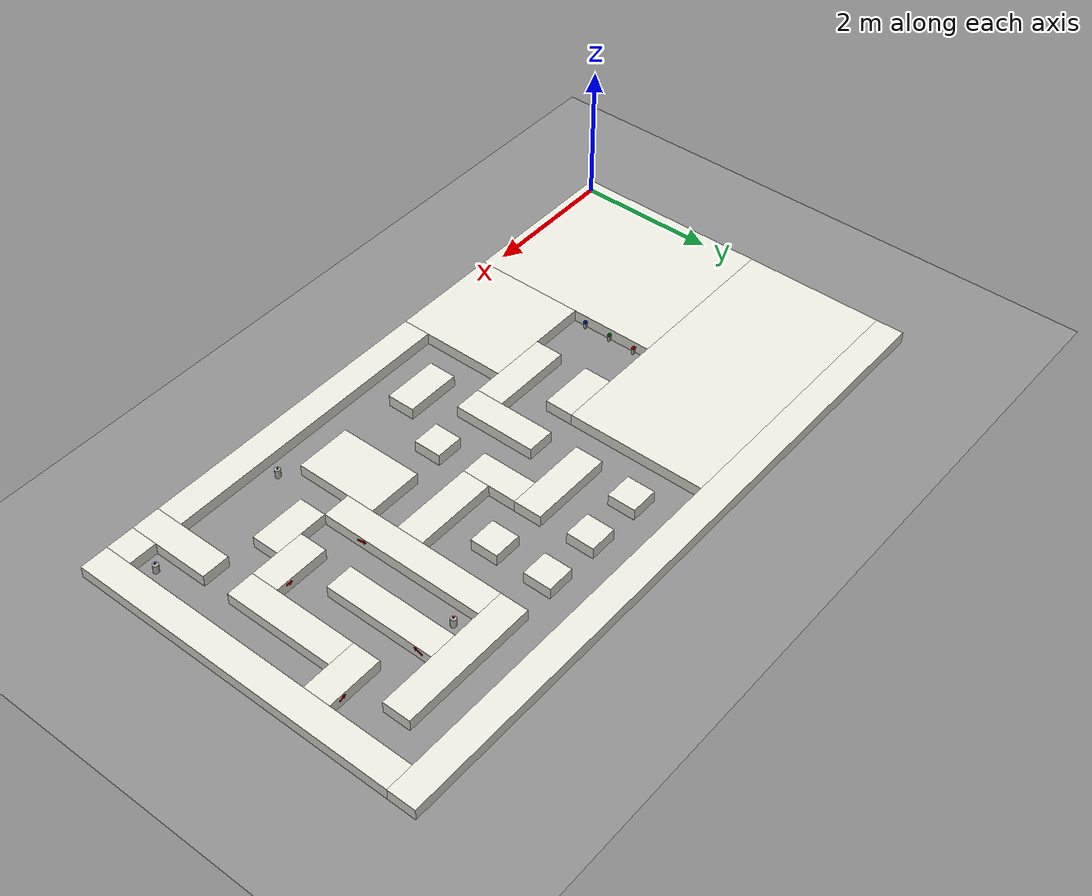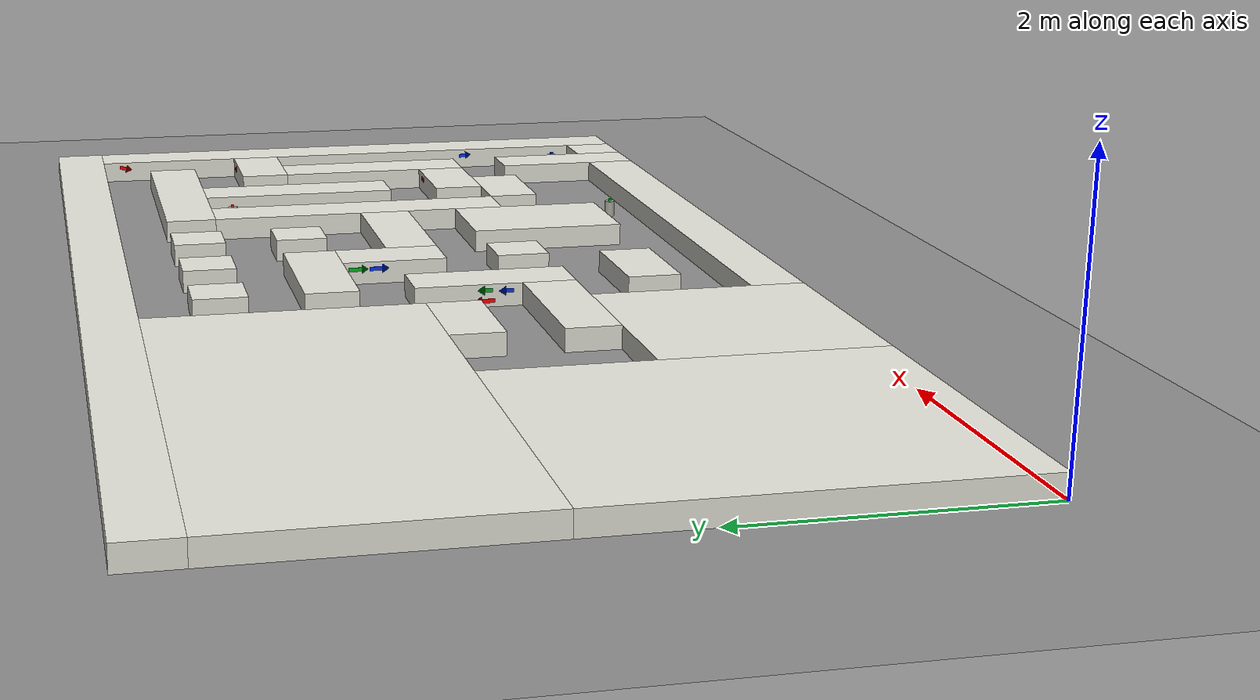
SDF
<?xml version="1.0"?>
<!-- Generado por gen_maze.py a partir de mazes/e6_salida_abierta_simple.yaml. No editar a mano: editar el YAML y regenerar. -->
<!-- E6 Salida abierta: laberinto grande, sala abierta y entrada entre paredes (simple: sin flechas laterales ni zonas) -->
<!-- Inicio del robot: x=3 y=2.2 yaw=0 -->
<sdf version="1.9">
  <world name="ros2_world">

    <plugin filename="gz-sim-physics-system"
            name="gz::sim::systems::Physics"/>

    <plugin filename="gz-sim-user-commands-system"
            name="gz::sim::systems::UserCommands"/>

    <plugin filename="gz-sim-scene-broadcaster-system"
            name="gz::sim::systems::SceneBroadcaster"/>

    <plugin filename="gz-sim-sensors-system"
            name="gz::sim::systems::Sensors">
      <render_engine>ogre2</render_engine>
    </plugin>

    <light type="directional" name="sun">
      <pose>0 0 10 0 0 0</pose>
      <diffuse>0.8 0.8 0.8 1</diffuse>
      <specular>0.2 0.2 0.2 1</specular>
      <direction>-0.5 0.1 -0.9</direction>
    </light>

    <model name="ground_plane">
      <static>true</static>
      <link name="link">
        <collision name="collision">
          <geometry>
            <plane>
              <normal>0 0 1</normal>
              <size>30 30</size>
            </plane>
          </geometry>
        </collision>
        <visual name="visual">
          <geometry>
            <plane>
              <normal>0 0 1</normal>
              <size>30 30</size>
            </plane>
          </geometry>
          <material>
            <ambient>0.55 0.55 0.55 1</ambient>
            <diffuse>0.55 0.55 0.55 1</diffuse>
          </material>
        </visual>
      </link>
    </model>

    <model name="paredes">
      <static>true</static>
      <link name="bloque_0">
        <pose>4.8 5 0.085 0 0 0</pose>
        <collision name="colision">
          <pose>0 0 0 0 0 0</pose>
          <geometry><box><size>9.6 0.4 0.17</size></box></geometry>
        </collision>
        <visual name="visual">
          <pose>0 0 0 0 0 0</pose>
          <geometry><box><size>9.6 0.4 0.17</size></box></geometry>
          <material>
            <ambient>0.9 0.9 0.86 1</ambient>
            <diffuse>0.9 0.9 0.86 1</diffuse>
          </material>
        </visual>
      </link>
      <link name="bloque_1">
        <pose>2 3.8 0.085 0 0 0</pose>
        <collision name="colision">
          <pose>0 0 0 0 0 0</pose>
          <geometry><box><size>4 2 0.17</size></box></geometry>
        </collision>
        <visual name="visual">
          <pose>0 0 0 0 0 0</pose>
          <geometry><box><size>4 2 0.17</size></box></geometry>
          <material>
            <ambient>0.9 0.9 0.86 1</ambient>
            <diffuse>0.9 0.9 0.86 1</diffuse>
          </material>
        </visual>
      </link>
      <link name="bloque_2">
        <pose>9.4 2.4 0.085 0 0 0</pose>
        <collision name="colision">
          <pose>0 0 0 0 0 0</pose>
          <geometry><box><size>0.4 4.8 0.17</size></box></geometry>
        </collision>
        <visual name="visual">
          <pose>0 0 0 0 0 0</pose>
          <geometry><box><size>0.4 4.8 0.17</size></box></geometry>
          <material>
            <ambient>0.9 0.9 0.86 1</ambient>
            <diffuse>0.9 0.9 0.86 1</diffuse>
          </material>
        </visual>
      </link>
      <link name="bloque_3">
        <pose>4.6 4.2 0.085 0 0 0</pose>
        <collision name="colision">
          <pose>0 0 0 0 0 0</pose>
          <geometry><box><size>0.4 0.4 0.17</size></box></geometry>
        </collision>
        <visual name="visual">
          <pose>0 0 0 0 0 0</pose>
          <geometry><box><size>0.4 0.4 0.17</size></box></geometry>
          <material>
            <ambient>0.9 0.9 0.86 1</ambient>
            <diffuse>0.9 0.9 0.86 1</diffuse>
          </material>
        </visual>
      </link>
      <link name="bloque_4">
        <pose>5.4 4.2 0.085 0 0 0</pose>
        <collision name="colision">
          <pose>0 0 0 0 0 0</pose>
          <geometry><box><size>0.4 0.4 0.17</size></box></geometry>
        </collision>
        <visual name="visual">
          <pose>0 0 0 0 0 0</pose>
          <geometry><box><size>0.4 0.4 0.17</size></box></geometry>
          <material>
            <ambient>0.9 0.9 0.86 1</ambient>
            <diffuse>0.9 0.9 0.86 1</diffuse>
          </material>
        </visual>
      </link>
      <link name="bloque_5">
        <pose>6.2 4.2 0.085 0 0 0</pose>
        <collision name="colision">
          <pose>0 0 0 0 0 0</pose>
          <geometry><box><size>0.4 0.4 0.17</size></box></geometry>
        </collision>
        <visual name="visual">
          <pose>0 0 0 0 0 0</pose>
          <geometry><box><size>0.4 0.4 0.17</size></box></geometry>
          <material>
            <ambient>0.9 0.9 0.86 1</ambient>
            <diffuse>0.9 0.9 0.86 1</diffuse>
          </material>
        </visual>
      </link>
      <link name="bloque_6">
        <pose>7.8 4.2 0.085 0 0 0</pose>
        <collision name="colision">
          <pose>0 0 0 0 0 0</pose>
          <geometry><box><size>2 0.4 0.17</size></box></geometry>
        </collision>
        <visual name="visual">
          <pose>0 0 0 0 0 0</pose>
          <geometry><box><size>2 0.4 0.17</size></box></geometry>
          <material>
            <ambient>0.9 0.9 0.86 1</ambient>
            <diffuse>0.9 0.9 0.86 1</diffuse>
          </material>
        </visual>
      </link>
      <link name="bloque_7">
        <pose>7 2.8 0.085 0 0 0</pose>
        <collision name="colision">
          <pose>0 0 0 0 0 0</pose>
          <geometry><box><size>0.4 2.4 0.17</size></box></geometry>
        </collision>
        <visual name="visual">
          <pose>0 0 0 0 0 0</pose>
          <geometry><box><size>0.4 2.4 0.17</size></box></geometry>
          <material>
            <ambient>0.9 0.9 0.86 1</ambient>
            <diffuse>0.9 0.9 0.86 1</diffuse>
          </material>
        </visual>
      </link>
      <link name="bloque_8">
        <pose>7.8 3.2 0.085 0 0 0</pose>
        <collision name="colision">
          <pose>0 0 0 0 0 0</pose>
          <geometry><box><size>0.4 1.6 0.17</size></box></geometry>
        </collision>
        <visual name="visual">
          <pose>0 0 0 0 0 0</pose>
          <geometry><box><size>0.4 1.6 0.17</size></box></geometry>
          <material>
            <ambient>0.9 0.9 0.86 1</ambient>
            <diffuse>0.9 0.9 0.86 1</diffuse>
          </material>
        </visual>
      </link>
      <link name="bloque_9">
        <pose>5 3.4 0.085 0 0 0</pose>
        <collision name="colision">
          <pose>0 0 0 0 0 0</pose>
          <geometry><box><size>1.2 0.4 0.17</size></box></geometry>
        </collision>
        <visual name="visual">
          <pose>0 0 0 0 0 0</pose>
          <geometry><box><size>1.2 0.4 0.17</size></box></geometry>
          <material>
            <ambient>0.9 0.9 0.86 1</ambient>
            <diffuse>0.9 0.9 0.86 1</diffuse>
          </material>
        </visual>
      </link>
      <link name="bloque_10">
        <pose>6.2 3.4 0.085 0 0 0</pose>
        <collision name="colision">
          <pose>0 0 0 0 0 0</pose>
          <geometry><box><size>0.4 0.4 0.17</size></box></geometry>
        </collision>
        <visual name="visual">
          <pose>0 0 0 0 0 0</pose>
          <geometry><box><size>0.4 0.4 0.17</size></box></geometry>
          <material>
            <ambient>0.9 0.9 0.86 1</ambient>
            <diffuse>0.9 0.9 0.86 1</diffuse>
          </material>
        </visual>
      </link>
      <link name="bloque_11">
        <pose>8.8 3.4 0.085 0 0 0</pose>
        <collision name="colision">
          <pose>0 0 0 0 0 0</pose>
          <geometry><box><size>0.8 0.4 0.17</size></box></geometry>
        </collision>
        <visual name="visual">
          <pose>0 0 0 0 0 0</pose>
          <geometry><box><size>0.8 0.4 0.17</size></box></geometry>
          <material>
            <ambient>0.9 0.9 0.86 1</ambient>
            <diffuse>0.9 0.9 0.86 1</diffuse>
          </material>
        </visual>
      </link>
      <link name="bloque_12">
        <pose>5.4 2.8 0.085 0 0 0</pose>
        <collision name="colision">
          <pose>0 0 0 0 0 0</pose>
          <geometry><box><size>0.4 0.8 0.17</size></box></geometry>
        </collision>
        <visual name="visual">
          <pose>0 0 0 0 0 0</pose>
          <geometry><box><size>0.4 0.8 0.17</size></box></geometry>
          <material>
            <ambient>0.9 0.9 0.86 1</ambient>
            <diffuse>0.9 0.9 0.86 1</diffuse>
          </material>
        </visual>
      </link>
      <link name="bloque_13">
        <pose>8.6 2.4 0.085 0 0 0</pose>
        <collision name="colision">
          <pose>0 0 0 0 0 0</pose>
          <geometry><box><size>0.4 1.6 0.17</size></box></geometry>
        </collision>
        <visual name="visual">
          <pose>0 0 0 0 0 0</pose>
          <geometry><box><size>0.4 1.6 0.17</size></box></geometry>
          <material>
            <ambient>0.9 0.9 0.86 1</ambient>
            <diffuse>0.9 0.9 0.86 1</diffuse>
          </material>
        </visual>
      </link>
      <link name="bloque_14">
        <pose>1.2 1.4 0.085 0 0 0</pose>
        <collision name="colision">
          <pose>0 0 0 0 0 0</pose>
          <geometry><box><size>2.4 2.8 0.17</size></box></geometry>
        </collision>
        <visual name="visual">
          <pose>0 0 0 0 0 0</pose>
          <geometry><box><size>2.4 2.8 0.17</size></box></geometry>
          <material>
            <ambient>0.9 0.9 0.86 1</ambient>
            <diffuse>0.9 0.9 0.86 1</diffuse>
          </material>
        </visual>
      </link>
      <link name="bloque_15">
        <pose>3.6 2.6 0.085 0 0 0</pose>
        <collision name="colision">
          <pose>0 0 0 0 0 0</pose>
          <geometry><box><size>0.8 0.4 0.17</size></box></geometry>
        </collision>
        <visual name="visual">
          <pose>0 0 0 0 0 0</pose>
          <geometry><box><size>0.8 0.4 0.17</size></box></geometry>
          <material>
            <ambient>0.9 0.9 0.86 1</ambient>
            <diffuse>0.9 0.9 0.86 1</diffuse>
          </material>
        </visual>
      </link>
      <link name="bloque_16">
        <pose>4.6 2.2 0.085 0 0 0</pose>
        <collision name="colision">
          <pose>0 0 0 0 0 0</pose>
          <geometry><box><size>0.4 1.2 0.17</size></box></geometry>
        </collision>
        <visual name="visual">
          <pose>0 0 0 0 0 0</pose>
          <geometry><box><size>0.4 1.2 0.17</size></box></geometry>
          <material>
            <ambient>0.9 0.9 0.86 1</ambient>
            <diffuse>0.9 0.9 0.86 1</diffuse>
          </material>
        </visual>
      </link>
      <link name="bloque_17">
        <pose>6.2 2.6 0.085 0 0 0</pose>
        <collision name="colision">
          <pose>0 0 0 0 0 0</pose>
          <geometry><box><size>1.2 0.4 0.17</size></box></geometry>
        </collision>
        <visual name="visual">
          <pose>0 0 0 0 0 0</pose>
          <geometry><box><size>1.2 0.4 0.17</size></box></geometry>
          <material>
            <ambient>0.9 0.9 0.86 1</ambient>
            <diffuse>0.9 0.9 0.86 1</diffuse>
          </material>
        </visual>
      </link>
      <link name="bloque_18">
        <pose>3.8 1.8 0.085 0 0 0</pose>
        <collision name="colision">
          <pose>0 0 0 0 0 0</pose>
          <geometry><box><size>1.2 0.4 0.17</size></box></geometry>
        </collision>
        <visual name="visual">
          <pose>0 0 0 0 0 0</pose>
          <geometry><box><size>1.2 0.4 0.17</size></box></geometry>
          <material>
            <ambient>0.9 0.9 0.86 1</ambient>
            <diffuse>0.9 0.9 0.86 1</diffuse>
          </material>
        </visual>
      </link>
      <link name="bloque_19">
        <pose>5.4 1.8 0.085 0 0 0</pose>
        <collision name="colision">
          <pose>0 0 0 0 0 0</pose>
          <geometry><box><size>0.4 0.4 0.17</size></box></geometry>
        </collision>
        <visual name="visual">
          <pose>0 0 0 0 0 0</pose>
          <geometry><box><size>0.4 0.4 0.17</size></box></geometry>
          <material>
            <ambient>0.9 0.9 0.86 1</ambient>
            <diffuse>0.9 0.9 0.86 1</diffuse>
          </material>
        </visual>
      </link>
      <link name="bloque_20">
        <pose>6.4 1.4 0.085 0 0 0</pose>
        <collision name="colision">
          <pose>0 0 0 0 0 0</pose>
          <geometry><box><size>0.8 1.2 0.17</size></box></geometry>
        </collision>
        <visual name="visual">
          <pose>0 0 0 0 0 0</pose>
          <geometry><box><size>0.8 1.2 0.17</size></box></geometry>
          <material>
            <ambient>0.9 0.9 0.86 1</ambient>
            <diffuse>0.9 0.9 0.86 1</diffuse>
          </material>
        </visual>
      </link>
      <link name="bloque_21">
        <pose>8 1.8 0.085 0 0 0</pose>
        <collision name="colision">
          <pose>0 0 0 0 0 0</pose>
          <geometry><box><size>0.8 0.4 0.17</size></box></geometry>
        </collision>
        <visual name="visual">
          <pose>0 0 0 0 0 0</pose>
          <geometry><box><size>0.8 0.4 0.17</size></box></geometry>
          <material>
            <ambient>0.9 0.9 0.86 1</ambient>
            <diffuse>0.9 0.9 0.86 1</diffuse>
          </material>
        </visual>
      </link>
      <link name="bloque_22">
        <pose>3.2 0.8 0.085 0 0 0</pose>
        <collision name="colision">
          <pose>0 0 0 0 0 0</pose>
          <geometry><box><size>1.6 1.6 0.17</size></box></geometry>
        </collision>
        <visual name="visual">
          <pose>0 0 0 0 0 0</pose>
          <geometry><box><size>1.6 1.6 0.17</size></box></geometry>
          <material>
            <ambient>0.9 0.9 0.86 1</ambient>
            <diffuse>0.9 0.9 0.86 1</diffuse>
          </material>
        </visual>
      </link>
      <link name="bloque_23">
        <pose>7.6 1.4 0.085 0 0 0</pose>
        <collision name="colision">
          <pose>0 0 0 0 0 0</pose>
          <geometry><box><size>0.8 0.4 0.17</size></box></geometry>
        </collision>
        <visual name="visual">
          <pose>0 0 0 0 0 0</pose>
          <geometry><box><size>0.8 0.4 0.17</size></box></geometry>
          <material>
            <ambient>0.9 0.9 0.86 1</ambient>
            <diffuse>0.9 0.9 0.86 1</diffuse>
          </material>
        </visual>
      </link>
      <link name="bloque_24">
        <pose>4.8 1 0.085 0 0 0</pose>
        <collision name="colision">
          <pose>0 0 0 0 0 0</pose>
          <geometry><box><size>0.8 0.4 0.17</size></box></geometry>
        </collision>
        <visual name="visual">
          <pose>0 0 0 0 0 0</pose>
          <geometry><box><size>0.8 0.4 0.17</size></box></geometry>
          <material>
            <ambient>0.9 0.9 0.86 1</ambient>
            <diffuse>0.9 0.9 0.86 1</diffuse>
          </material>
        </visual>
      </link>
      <link name="bloque_25">
        <pose>8.6 0.6 0.085 0 0 0</pose>
        <collision name="colision">
          <pose>0 0 0 0 0 0</pose>
          <geometry><box><size>0.4 1.2 0.17</size></box></geometry>
        </collision>
        <visual name="visual">
          <pose>0 0 0 0 0 0</pose>
          <geometry><box><size>0.4 1.2 0.17</size></box></geometry>
          <material>
            <ambient>0.9 0.9 0.86 1</ambient>
            <diffuse>0.9 0.9 0.86 1</diffuse>
          </material>
        </visual>
      </link>
      <link name="bloque_26">
        <pose>6.2 0.2 0.085 0 0 0</pose>
        <collision name="colision">
          <pose>0 0 0 0 0 0</pose>
          <geometry><box><size>4.4 0.4 0.17</size></box></geometry>
        </collision>
        <visual name="visual">
          <pose>0 0 0 0 0 0</pose>
          <geometry><box><size>4.4 0.4 0.17</size></box></geometry>
          <material>
            <ambient>0.9 0.9 0.86 1</ambient>
            <diffuse>0.9 0.9 0.86 1</diffuse>
          </material>
        </visual>
      </link>
      <link name="bloque_27">
        <pose>9 0.2 0.085 0 0 0</pose>
        <collision name="colision">
          <pose>0 0 0 0 0 0</pose>
          <geometry><box><size>0.4 0.4 0.17</size></box></geometry>
        </collision>
        <visual name="visual">
          <pose>0 0 0 0 0 0</pose>
          <geometry><box><size>0.4 0.4 0.17</size></box></geometry>
          <material>
            <ambient>0.9 0.9 0.86 1</ambient>
            <diffuse>0.9 0.9 0.86 1</diffuse>
          </material>
        </visual>
      </link>
    </model>

    <model name="flechas">
      <static>true</static>
      <link name="flecha_0">
        <pose>4.2 4.7985 0.115 0 0 0</pose>
        <visual name="p0">
          <pose>-0.025 0 0 0 0 0</pose>
          <geometry><box><size>0.1 0.002 0.03</size></box></geometry>
          <material>
            <ambient>1 0 0 1</ambient>
            <diffuse>1 0 0 1</diffuse>
          </material>
        </visual>
        <visual name="p1">
          <pose>0.026 0 0 0 0 0</pose>
          <geometry><box><size>0.002 0.002 0.07</size></box></geometry>
          <material>
            <ambient>1 0 0 1</ambient>
            <diffuse>1 0 0 1</diffuse>
          </material>
        </visual>
        <visual name="p2">
          <pose>0.028 0 0 0 0 0</pose>
          <geometry><box><size>0.002 0.002 0.0672</size></box></geometry>
          <material>
            <ambient>1 0 0 1</ambient>
            <diffuse>1 0 0 1</diffuse>
          </material>
        </visual>
        <visual name="p3">
          <pose>0.03 0 0 0 0 0</pose>
          <geometry><box><size>0.002 0.002 0.0644</size></box></geometry>
          <material>
            <ambient>1 0 0 1</ambient>
            <diffuse>1 0 0 1</diffuse>
          </material>
        </visual>
        <visual name="p4">
          <pose>0.032 0 0 0 0 0</pose>
          <geometry><box><size>0.002 0.002 0.0616</size></box></geometry>
          <material>
            <ambient>1 0 0 1</ambient>
            <diffuse>1 0 0 1</diffuse>
          </material>
        </visual>
        <visual name="p5">
          <pose>0.034 0 0 0 0 0</pose>
          <geometry><box><size>0.002 0.002 0.0588</size></box></geometry>
          <material>
            <ambient>1 0 0 1</ambient>
            <diffuse>1 0 0 1</diffuse>
          </material>
        </visual>
        <visual name="p6">
          <pose>0.036 0 0 0 0 0</pose>
          <geometry><box><size>0.002 0.002 0.056</size></box></geometry>
          <material>
            <ambient>1 0 0 1</ambient>
            <diffuse>1 0 0 1</diffuse>
          </material>
        </visual>
        <visual name="p7">
          <pose>0.038 0 0 0 0 0</pose>
          <geometry><box><size>0.002 0.002 0.0532</size></box></geometry>
          <material>
            <ambient>1 0 0 1</ambient>
            <diffuse>1 0 0 1</diffuse>
          </material>
        </visual>
        <visual name="p8">
          <pose>0.04 0 0 0 0 0</pose>
          <geometry><box><size>0.002 0.002 0.0504</size></box></geometry>
          <material>
            <ambient>1 0 0 1</ambient>
            <diffuse>1 0 0 1</diffuse>
          </material>
        </visual>
        <visual name="p9">
          <pose>0.042 0 0 0 0 0</pose>
          <geometry><box><size>0.002 0.002 0.0476</size></box></geometry>
          <material>
            <ambient>1 0 0 1</ambient>
            <diffuse>1 0 0 1</diffuse>
          </material>
        </visual>
        <visual name="p10">
          <pose>0.044 0 0 0 0 0</pose>
          <geometry><box><size>0.002 0.002 0.0448</size></box></geometry>
          <material>
            <ambient>1 0 0 1</ambient>
            <diffuse>1 0 0 1</diffuse>
          </material>
        </visual>
        <visual name="p11">
          <pose>0.046 0 0 0 0 0</pose>
          <geometry><box><size>0.002 0.002 0.042</size></box></geometry>
          <material>
            <ambient>1 0 0 1</ambient>
            <diffuse>1 0 0 1</diffuse>
          </material>
        </visual>
        <visual name="p12">
          <pose>0.048 0 0 0 0 0</pose>
          <geometry><box><size>0.002 0.002 0.0392</size></box></geometry>
          <material>
            <ambient>1 0 0 1</ambient>
            <diffuse>1 0 0 1</diffuse>
          </material>
        </visual>
        <visual name="p13">
          <pose>0.05 0 0 0 0 0</pose>
          <geometry><box><size>0.002 0.002 0.0364</size></box></geometry>
          <material>
            <ambient>1 0 0 1</ambient>
            <diffuse>1 0 0 1</diffuse>
          </material>
        </visual>
        <visual name="p14">
          <pose>0.052 0 0 0 0 0</pose>
          <geometry><box><size>0.002 0.002 0.0336</size></box></geometry>
          <material>
            <ambient>1 0 0 1</ambient>
            <diffuse>1 0 0 1</diffuse>
          </material>
        </visual>
        <visual name="p15">
          <pose>0.054 0 0 0 0 0</pose>
          <geometry><box><size>0.002 0.002 0.0308</size></box></geometry>
          <material>
            <ambient>1 0 0 1</ambient>
            <diffuse>1 0 0 1</diffuse>
          </material>
        </visual>
        <visual name="p16">
          <pose>0.056 0 0 0 0 0</pose>
          <geometry><box><size>0.002 0.002 0.028</size></box></geometry>
          <material>
            <ambient>1 0 0 1</ambient>
            <diffuse>1 0 0 1</diffuse>
          </material>
        </visual>
        <visual name="p17">
          <pose>0.058 0 0 0 0 0</pose>
          <geometry><box><size>0.002 0.002 0.0252</size></box></geometry>
          <material>
            <ambient>1 0 0 1</ambient>
            <diffuse>1 0 0 1</diffuse>
          </material>
        </visual>
        <visual name="p18">
          <pose>0.06 0 0 0 0 0</pose>
          <geometry><box><size>0.002 0.002 0.0224</size></box></geometry>
          <material>
            <ambient>1 0 0 1</ambient>
            <diffuse>1 0 0 1</diffuse>
          </material>
        </visual>
        <visual name="p19">
          <pose>0.062 0 0 0 0 0</pose>
          <geometry><box><size>0.002 0.002 0.0196</size></box></geometry>
          <material>
            <ambient>1 0 0 1</ambient>
            <diffuse>1 0 0 1</diffuse>
          </material>
        </visual>
        <visual name="p20">
          <pose>0.064 0 0 0 0 0</pose>
          <geometry><box><size>0.002 0.002 0.0168</size></box></geometry>
          <material>
            <ambient>1 0 0 1</ambient>
            <diffuse>1 0 0 1</diffuse>
          </material>
        </visual>
        <visual name="p21">
          <pose>0.066 0 0 0 0 0</pose>
          <geometry><box><size>0.002 0.002 0.014</size></box></geometry>
          <material>
            <ambient>1 0 0 1</ambient>
            <diffuse>1 0 0 1</diffuse>
          </material>
        </visual>
        <visual name="p22">
          <pose>0.068 0 0 0 0 0</pose>
          <geometry><box><size>0.002 0.002 0.0112</size></box></geometry>
          <material>
            <ambient>1 0 0 1</ambient>
            <diffuse>1 0 0 1</diffuse>
          </material>
        </visual>
        <visual name="p23">
          <pose>0.07 0 0 0 0 0</pose>
          <geometry><box><size>0.002 0.002 0.0084</size></box></geometry>
          <material>
            <ambient>1 0 0 1</ambient>
            <diffuse>1 0 0 1</diffuse>
          </material>
        </visual>
        <visual name="p24">
          <pose>0.072 0 0 0 0 0</pose>
          <geometry><box><size>0.002 0.002 0.0056</size></box></geometry>
          <material>
            <ambient>1 0 0 1</ambient>
            <diffuse>1 0 0 1</diffuse>
          </material>
        </visual>
        <visual name="p25">
          <pose>0.074 0 0 0 0 0</pose>
          <geometry><box><size>0.002 0.002 0.0028</size></box></geometry>
          <material>
            <ambient>1 0 0 1</ambient>
            <diffuse>1 0 0 1</diffuse>
          </material>
        </visual>
      </link>
      <link name="flecha_1">
        <pose>9.1985 4.6 0.115 0 0.2618 -1.5708</pose>
        <visual name="p0">
          <pose>-0.025 0 0 0 0 0</pose>
          <geometry><box><size>0.06 0.002 0.03</size></box></geometry>
          <material>
            <ambient>1 0 0 1</ambient>
            <diffuse>1 0 0 1</diffuse>
          </material>
        </visual>
        <visual name="p1">
          <pose>0.006 0 0 0 0 0</pose>
          <geometry><box><size>0.002 0.002 0.07</size></box></geometry>
          <material>
            <ambient>1 0 0 1</ambient>
            <diffuse>1 0 0 1</diffuse>
          </material>
        </visual>
        <visual name="p2">
          <pose>0.008 0 0 0 0 0</pose>
          <geometry><box><size>0.002 0.002 0.0672</size></box></geometry>
          <material>
            <ambient>1 0 0 1</ambient>
            <diffuse>1 0 0 1</diffuse>
          </material>
        </visual>
        <visual name="p3">
          <pose>0.01 0 0 0 0 0</pose>
          <geometry><box><size>0.002 0.002 0.0644</size></box></geometry>
          <material>
            <ambient>1 0 0 1</ambient>
            <diffuse>1 0 0 1</diffuse>
          </material>
        </visual>
        <visual name="p4">
          <pose>0.012 0 0 0 0 0</pose>
          <geometry><box><size>0.002 0.002 0.0616</size></box></geometry>
          <material>
            <ambient>1 0 0 1</ambient>
            <diffuse>1 0 0 1</diffuse>
          </material>
        </visual>
        <visual name="p5">
          <pose>0.014 0 0 0 0 0</pose>
          <geometry><box><size>0.002 0.002 0.0588</size></box></geometry>
          <material>
            <ambient>1 0 0 1</ambient>
            <diffuse>1 0 0 1</diffuse>
          </material>
        </visual>
        <visual name="p6">
          <pose>0.016 0 0 0 0 0</pose>
          <geometry><box><size>0.002 0.002 0.056</size></box></geometry>
          <material>
            <ambient>1 0 0 1</ambient>
            <diffuse>1 0 0 1</diffuse>
          </material>
        </visual>
        <visual name="p7">
          <pose>0.018 0 0 0 0 0</pose>
          <geometry><box><size>0.002 0.002 0.0532</size></box></geometry>
          <material>
            <ambient>1 0 0 1</ambient>
            <diffuse>1 0 0 1</diffuse>
          </material>
        </visual>
        <visual name="p8">
          <pose>0.02 0 0 0 0 0</pose>
          <geometry><box><size>0.002 0.002 0.0504</size></box></geometry>
          <material>
            <ambient>1 0 0 1</ambient>
            <diffuse>1 0 0 1</diffuse>
          </material>
        </visual>
        <visual name="p9">
          <pose>0.022 0 0 0 0 0</pose>
          <geometry><box><size>0.002 0.002 0.0476</size></box></geometry>
          <material>
            <ambient>1 0 0 1</ambient>
            <diffuse>1 0 0 1</diffuse>
          </material>
        </visual>
        <visual name="p10">
          <pose>0.024 0 0 0 0 0</pose>
          <geometry><box><size>0.002 0.002 0.0448</size></box></geometry>
          <material>
            <ambient>1 0 0 1</ambient>
            <diffuse>1 0 0 1</diffuse>
          </material>
        </visual>
        <visual name="p11">
          <pose>0.026 0 0 0 0 0</pose>
          <geometry><box><size>0.002 0.002 0.042</size></box></geometry>
          <material>
            <ambient>1 0 0 1</ambient>
            <diffuse>1 0 0 1</diffuse>
          </material>
        </visual>
        <visual name="p12">
          <pose>0.028 0 0 0 0 0</pose>
          <geometry><box><size>0.002 0.002 0.0392</size></box></geometry>
          <material>
            <ambient>1 0 0 1</ambient>
            <diffuse>1 0 0 1</diffuse>
          </material>
        </visual>
        <visual name="p13">
          <pose>0.03 0 0 0 0 0</pose>
          <geometry><box><size>0.002 0.002 0.0364</size></box></geometry>
          <material>
            <ambient>1 0 0 1</ambient>
            <diffuse>1 0 0 1</diffuse>
          </material>
        </visual>
        <visual name="p14">
          <pose>0.032 0 0 0 0 0</pose>
          <geometry><box><size>0.002 0.002 0.0336</size></box></geometry>
          <material>
            <ambient>1 0 0 1</ambient>
            <diffuse>1 0 0 1</diffuse>
          </material>
        </visual>
        <visual name="p15">
          <pose>0.034 0 0 0 0 0</pose>
          <geometry><box><size>0.002 0.002 0.0308</size></box></geometry>
          <material>
            <ambient>1 0 0 1</ambient>
            <diffuse>1 0 0 1</diffuse>
          </material>
        </visual>
        <visual name="p16">
          <pose>0.036 0 0 0 0 0</pose>
          <geometry><box><size>0.002 0.002 0.028</size></box></geometry>
          <material>
            <ambient>1 0 0 1</ambient>
            <diffuse>1 0 0 1</diffuse>
          </material>
        </visual>
        <visual name="p17">
          <pose>0.038 0 0 0 0 0</pose>
          <geometry><box><size>0.002 0.002 0.0252</size></box></geometry>
          <material>
            <ambient>1 0 0 1</ambient>
            <diffuse>1 0 0 1</diffuse>
          </material>
        </visual>
        <visual name="p18">
          <pose>0.04 0 0 0 0 0</pose>
          <geometry><box><size>0.002 0.002 0.0224</size></box></geometry>
          <material>
            <ambient>1 0 0 1</ambient>
            <diffuse>1 0 0 1</diffuse>
          </material>
        </visual>
        <visual name="p19">
          <pose>0.042 0 0 0 0 0</pose>
          <geometry><box><size>0.002 0.002 0.0196</size></box></geometry>
          <material>
            <ambient>1 0 0 1</ambient>
            <diffuse>1 0 0 1</diffuse>
          </material>
        </visual>
        <visual name="p20">
          <pose>0.044 0 0 0 0 0</pose>
          <geometry><box><size>0.002 0.002 0.0168</size></box></geometry>
          <material>
            <ambient>1 0 0 1</ambient>
            <diffuse>1 0 0 1</diffuse>
          </material>
        </visual>
        <visual name="p21">
          <pose>0.046 0 0 0 0 0</pose>
          <geometry><box><size>0.002 0.002 0.014</size></box></geometry>
          <material>
            <ambient>1 0 0 1</ambient>
            <diffuse>1 0 0 1</diffuse>
          </material>
        </visual>
        <visual name="p22">
          <pose>0.048 0 0 0 0 0</pose>
          <geometry><box><size>0.002 0.002 0.0112</size></box></geometry>
          <material>
            <ambient>1 0 0 1</ambient>
            <diffuse>1 0 0 1</diffuse>
          </material>
        </visual>
        <visual name="p23">
          <pose>0.05 0 0 0 0 0</pose>
          <geometry><box><size>0.002 0.002 0.0084</size></box></geometry>
          <material>
            <ambient>1 0 0 1</ambient>
            <diffuse>1 0 0 1</diffuse>
          </material>
        </visual>
        <visual name="p24">
          <pose>0.052 0 0 0 0 0</pose>
          <geometry><box><size>0.002 0.002 0.0056</size></box></geometry>
          <material>
            <ambient>1 0 0 1</ambient>
            <diffuse>1 0 0 1</diffuse>
          </material>
        </visual>
        <visual name="p25">
          <pose>0.054 0 0 0 0 0</pose>
          <geometry><box><size>0.002 0.002 0.0028</size></box></geometry>
          <material>
            <ambient>1 0 0 1</ambient>
            <diffuse>1 0 0 1</diffuse>
          </material>
        </visual>
      </link>
      <link name="flecha_2">
        <pose>8.0015 3.8 0.115 0 -0.36652 -1.5708</pose>
        <visual name="p0">
          <pose>-0.025 0 0 0 0 0</pose>
          <geometry><box><size>0.1 0.002 0.03</size></box></geometry>
          <material>
            <ambient>1 0 0 1</ambient>
            <diffuse>1 0 0 1</diffuse>
          </material>
        </visual>
        <visual name="p1">
          <pose>0.026 0 0 0 0 0</pose>
          <geometry><box><size>0.002 0.002 0.07</size></box></geometry>
          <material>
            <ambient>1 0 0 1</ambient>
            <diffuse>1 0 0 1</diffuse>
          </material>
        </visual>
        <visual name="p2">
          <pose>0.028 0 0 0 0 0</pose>
          <geometry><box><size>0.002 0.002 0.0672</size></box></geometry>
          <material>
            <ambient>1 0 0 1</ambient>
            <diffuse>1 0 0 1</diffuse>
          </material>
        </visual>
        <visual name="p3">
          <pose>0.03 0 0 0 0 0</pose>
          <geometry><box><size>0.002 0.002 0.0644</size></box></geometry>
          <material>
            <ambient>1 0 0 1</ambient>
            <diffuse>1 0 0 1</diffuse>
          </material>
        </visual>
        <visual name="p4">
          <pose>0.032 0 0 0 0 0</pose>
          <geometry><box><size>0.002 0.002 0.0616</size></box></geometry>
          <material>
            <ambient>1 0 0 1</ambient>
            <diffuse>1 0 0 1</diffuse>
          </material>
        </visual>
        <visual name="p5">
          <pose>0.034 0 0 0 0 0</pose>
          <geometry><box><size>0.002 0.002 0.0588</size></box></geometry>
          <material>
            <ambient>1 0 0 1</ambient>
            <diffuse>1 0 0 1</diffuse>
          </material>
        </visual>
        <visual name="p6">
          <pose>0.036 0 0 0 0 0</pose>
          <geometry><box><size>0.002 0.002 0.056</size></box></geometry>
          <material>
            <ambient>1 0 0 1</ambient>
            <diffuse>1 0 0 1</diffuse>
          </material>
        </visual>
        <visual name="p7">
          <pose>0.038 0 0 0 0 0</pose>
          <geometry><box><size>0.002 0.002 0.0532</size></box></geometry>
          <material>
            <ambient>1 0 0 1</ambient>
            <diffuse>1 0 0 1</diffuse>
          </material>
        </visual>
        <visual name="p8">
          <pose>0.04 0 0 0 0 0</pose>
          <geometry><box><size>0.002 0.002 0.0504</size></box></geometry>
          <material>
            <ambient>1 0 0 1</ambient>
            <diffuse>1 0 0 1</diffuse>
          </material>
        </visual>
        <visual name="p9">
          <pose>0.042 0 0 0 0 0</pose>
          <geometry><box><size>0.002 0.002 0.0476</size></box></geometry>
          <material>
            <ambient>1 0 0 1</ambient>
            <diffuse>1 0 0 1</diffuse>
          </material>
        </visual>
        <visual name="p10">
          <pose>0.044 0 0 0 0 0</pose>
          <geometry><box><size>0.002 0.002 0.0448</size></box></geometry>
          <material>
            <ambient>1 0 0 1</ambient>
            <diffuse>1 0 0 1</diffuse>
          </material>
        </visual>
        <visual name="p11">
          <pose>0.046 0 0 0 0 0</pose>
          <geometry><box><size>0.002 0.002 0.042</size></box></geometry>
          <material>
            <ambient>1 0 0 1</ambient>
            <diffuse>1 0 0 1</diffuse>
          </material>
        </visual>
        <visual name="p12">
          <pose>0.048 0 0 0 0 0</pose>
          <geometry><box><size>0.002 0.002 0.0392</size></box></geometry>
          <material>
            <ambient>1 0 0 1</ambient>
            <diffuse>1 0 0 1</diffuse>
          </material>
        </visual>
        <visual name="p13">
          <pose>0.05 0 0 0 0 0</pose>
          <geometry><box><size>0.002 0.002 0.0364</size></box></geometry>
          <material>
            <ambient>1 0 0 1</ambient>
            <diffuse>1 0 0 1</diffuse>
          </material>
        </visual>
        <visual name="p14">
          <pose>0.052 0 0 0 0 0</pose>
          <geometry><box><size>0.002 0.002 0.0336</size></box></geometry>
          <material>
            <ambient>1 0 0 1</ambient>
            <diffuse>1 0 0 1</diffuse>
          </material>
        </visual>
        <visual name="p15">
          <pose>0.054 0 0 0 0 0</pose>
          <geometry><box><size>0.002 0.002 0.0308</size></box></geometry>
          <material>
            <ambient>1 0 0 1</ambient>
            <diffuse>1 0 0 1</diffuse>
          </material>
        </visual>
        <visual name="p16">
          <pose>0.056 0 0 0 0 0</pose>
          <geometry><box><size>0.002 0.002 0.028</size></box></geometry>
          <material>
            <ambient>1 0 0 1</ambient>
            <diffuse>1 0 0 1</diffuse>
          </material>
        </visual>
        <visual name="p17">
          <pose>0.058 0 0 0 0 0</pose>
          <geometry><box><size>0.002 0.002 0.0252</size></box></geometry>
          <material>
            <ambient>1 0 0 1</ambient>
            <diffuse>1 0 0 1</diffuse>
          </material>
        </visual>
        <visual name="p18">
          <pose>0.06 0 0 0 0 0</pose>
          <geometry><box><size>0.002 0.002 0.0224</size></box></geometry>
          <material>
            <ambient>1 0 0 1</ambient>
            <diffuse>1 0 0 1</diffuse>
          </material>
        </visual>
        <visual name="p19">
          <pose>0.062 0 0 0 0 0</pose>
          <geometry><box><size>0.002 0.002 0.0196</size></box></geometry>
          <material>
            <ambient>1 0 0 1</ambient>
            <diffuse>1 0 0 1</diffuse>
          </material>
        </visual>
        <visual name="p20">
          <pose>0.064 0 0 0 0 0</pose>
          <geometry><box><size>0.002 0.002 0.0168</size></box></geometry>
          <material>
            <ambient>1 0 0 1</ambient>
            <diffuse>1 0 0 1</diffuse>
          </material>
        </visual>
        <visual name="p21">
          <pose>0.066 0 0 0 0 0</pose>
          <geometry><box><size>0.002 0.002 0.014</size></box></geometry>
          <material>
            <ambient>1 0 0 1</ambient>
            <diffuse>1 0 0 1</diffuse>
          </material>
        </visual>
        <visual name="p22">
          <pose>0.068 0 0 0 0 0</pose>
          <geometry><box><size>0.002 0.002 0.0112</size></box></geometry>
          <material>
            <ambient>1 0 0 1</ambient>
            <diffuse>1 0 0 1</diffuse>
          </material>
        </visual>
        <visual name="p23">
          <pose>0.07 0 0 0 0 0</pose>
          <geometry><box><size>0.002 0.002 0.0084</size></box></geometry>
          <material>
            <ambient>1 0 0 1</ambient>
            <diffuse>1 0 0 1</diffuse>
          </material>
        </visual>
        <visual name="p24">
          <pose>0.072 0 0 0 0 0</pose>
          <geometry><box><size>0.002 0.002 0.0056</size></box></geometry>
          <material>
            <ambient>1 0 0 1</ambient>
            <diffuse>1 0 0 1</diffuse>
          </material>
        </visual>
        <visual name="p25">
          <pose>0.074 0 0 0 0 0</pose>
          <geometry><box><size>0.002 0.002 0.0028</size></box></geometry>
          <material>
            <ambient>1 0 0 1</ambient>
            <diffuse>1 0 0 1</diffuse>
          </material>
        </visual>
      </link>
      <link name="flecha_3">
        <pose>9 3.6015 0.115 0 -0.41888 3.14159</pose>
        <visual name="p0">
          <pose>-0.025 0 0 0 0 0</pose>
          <geometry><box><size>0.06 0.002 0.03</size></box></geometry>
          <material>
            <ambient>1 0 0 1</ambient>
            <diffuse>1 0 0 1</diffuse>
          </material>
        </visual>
        <visual name="p1">
          <pose>0.006 0 0 0 0 0</pose>
          <geometry><box><size>0.002 0.002 0.07</size></box></geometry>
          <material>
            <ambient>1 0 0 1</ambient>
            <diffuse>1 0 0 1</diffuse>
          </material>
        </visual>
        <visual name="p2">
          <pose>0.008 0 0 0 0 0</pose>
          <geometry><box><size>0.002 0.002 0.0672</size></box></geometry>
          <material>
            <ambient>1 0 0 1</ambient>
            <diffuse>1 0 0 1</diffuse>
          </material>
        </visual>
        <visual name="p3">
          <pose>0.01 0 0 0 0 0</pose>
          <geometry><box><size>0.002 0.002 0.0644</size></box></geometry>
          <material>
            <ambient>1 0 0 1</ambient>
            <diffuse>1 0 0 1</diffuse>
          </material>
        </visual>
        <visual name="p4">
          <pose>0.012 0 0 0 0 0</pose>
          <geometry><box><size>0.002 0.002 0.0616</size></box></geometry>
          <material>
            <ambient>1 0 0 1</ambient>
            <diffuse>1 0 0 1</diffuse>
          </material>
        </visual>
        <visual name="p5">
          <pose>0.014 0 0 0 0 0</pose>
          <geometry><box><size>0.002 0.002 0.0588</size></box></geometry>
          <material>
            <ambient>1 0 0 1</ambient>
            <diffuse>1 0 0 1</diffuse>
          </material>
        </visual>
        <visual name="p6">
          <pose>0.016 0 0 0 0 0</pose>
          <geometry><box><size>0.002 0.002 0.056</size></box></geometry>
          <material>
            <ambient>1 0 0 1</ambient>
            <diffuse>1 0 0 1</diffuse>
          </material>
        </visual>
        <visual name="p7">
          <pose>0.018 0 0 0 0 0</pose>
          <geometry><box><size>0.002 0.002 0.0532</size></box></geometry>
          <material>
            <ambient>1 0 0 1</ambient>
            <diffuse>1 0 0 1</diffuse>
          </material>
        </visual>
        <visual name="p8">
          <pose>0.02 0 0 0 0 0</pose>
          <geometry><box><size>0.002 0.002 0.0504</size></box></geometry>
          <material>
            <ambient>1 0 0 1</ambient>
            <diffuse>1 0 0 1</diffuse>
          </material>
        </visual>
        <visual name="p9">
          <pose>0.022 0 0 0 0 0</pose>
          <geometry><box><size>0.002 0.002 0.0476</size></box></geometry>
          <material>
            <ambient>1 0 0 1</ambient>
            <diffuse>1 0 0 1</diffuse>
          </material>
        </visual>
        <visual name="p10">
          <pose>0.024 0 0 0 0 0</pose>
          <geometry><box><size>0.002 0.002 0.0448</size></box></geometry>
          <material>
            <ambient>1 0 0 1</ambient>
            <diffuse>1 0 0 1</diffuse>
          </material>
        </visual>
        <visual name="p11">
          <pose>0.026 0 0 0 0 0</pose>
          <geometry><box><size>0.002 0.002 0.042</size></box></geometry>
          <material>
            <ambient>1 0 0 1</ambient>
            <diffuse>1 0 0 1</diffuse>
          </material>
        </visual>
        <visual name="p12">
          <pose>0.028 0 0 0 0 0</pose>
          <geometry><box><size>0.002 0.002 0.0392</size></box></geometry>
          <material>
            <ambient>1 0 0 1</ambient>
            <diffuse>1 0 0 1</diffuse>
          </material>
        </visual>
        <visual name="p13">
          <pose>0.03 0 0 0 0 0</pose>
          <geometry><box><size>0.002 0.002 0.0364</size></box></geometry>
          <material>
            <ambient>1 0 0 1</ambient>
            <diffuse>1 0 0 1</diffuse>
          </material>
        </visual>
        <visual name="p14">
          <pose>0.032 0 0 0 0 0</pose>
          <geometry><box><size>0.002 0.002 0.0336</size></box></geometry>
          <material>
            <ambient>1 0 0 1</ambient>
            <diffuse>1 0 0 1</diffuse>
          </material>
        </visual>
        <visual name="p15">
          <pose>0.034 0 0 0 0 0</pose>
          <geometry><box><size>0.002 0.002 0.0308</size></box></geometry>
          <material>
            <ambient>1 0 0 1</ambient>
            <diffuse>1 0 0 1</diffuse>
          </material>
        </visual>
        <visual name="p16">
          <pose>0.036 0 0 0 0 0</pose>
          <geometry><box><size>0.002 0.002 0.028</size></box></geometry>
          <material>
            <ambient>1 0 0 1</ambient>
            <diffuse>1 0 0 1</diffuse>
          </material>
        </visual>
        <visual name="p17">
          <pose>0.038 0 0 0 0 0</pose>
          <geometry><box><size>0.002 0.002 0.0252</size></box></geometry>
          <material>
            <ambient>1 0 0 1</ambient>
            <diffuse>1 0 0 1</diffuse>
          </material>
        </visual>
        <visual name="p18">
          <pose>0.04 0 0 0 0 0</pose>
          <geometry><box><size>0.002 0.002 0.0224</size></box></geometry>
          <material>
            <ambient>1 0 0 1</ambient>
            <diffuse>1 0 0 1</diffuse>
          </material>
        </visual>
        <visual name="p19">
          <pose>0.042 0 0 0 0 0</pose>
          <geometry><box><size>0.002 0.002 0.0196</size></box></geometry>
          <material>
            <ambient>1 0 0 1</ambient>
            <diffuse>1 0 0 1</diffuse>
          </material>
        </visual>
        <visual name="p20">
          <pose>0.044 0 0 0 0 0</pose>
          <geometry><box><size>0.002 0.002 0.0168</size></box></geometry>
          <material>
            <ambient>1 0 0 1</ambient>
            <diffuse>1 0 0 1</diffuse>
          </material>
        </visual>
        <visual name="p21">
          <pose>0.046 0 0 0 0 0</pose>
          <geometry><box><size>0.002 0.002 0.014</size></box></geometry>
          <material>
            <ambient>1 0 0 1</ambient>
            <diffuse>1 0 0 1</diffuse>
          </material>
        </visual>
        <visual name="p22">
          <pose>0.048 0 0 0 0 0</pose>
          <geometry><box><size>0.002 0.002 0.0112</size></box></geometry>
          <material>
            <ambient>1 0 0 1</ambient>
            <diffuse>1 0 0 1</diffuse>
          </material>
        </visual>
        <visual name="p23">
          <pose>0.05 0 0 0 0 0</pose>
          <geometry><box><size>0.002 0.002 0.0084</size></box></geometry>
          <material>
            <ambient>1 0 0 1</ambient>
            <diffuse>1 0 0 1</diffuse>
          </material>
        </visual>
        <visual name="p24">
          <pose>0.052 0 0 0 0 0</pose>
          <geometry><box><size>0.002 0.002 0.0056</size></box></geometry>
          <material>
            <ambient>1 0 0 1</ambient>
            <diffuse>1 0 0 1</diffuse>
          </material>
        </visual>
        <visual name="p25">
          <pose>0.054 0 0 0 0 0</pose>
          <geometry><box><size>0.002 0.002 0.0028</size></box></geometry>
          <material>
            <ambient>1 0 0 1</ambient>
            <diffuse>1 0 0 1</diffuse>
          </material>
        </visual>
      </link>
      <link name="flecha_4">
        <pose>5.1985 2.92 0.115 0 0 -1.5708</pose>
        <visual name="p0">
          <pose>-0.025 0 0 0 0 0</pose>
          <geometry><box><size>0.1 0.002 0.03</size></box></geometry>
          <material>
            <ambient>0 0.2 1 1</ambient>
            <diffuse>0 0.2 1 1</diffuse>
          </material>
        </visual>
        <visual name="p1">
          <pose>0.026 0 0 0 0 0</pose>
          <geometry><box><size>0.002 0.002 0.07</size></box></geometry>
          <material>
            <ambient>0 0.2 1 1</ambient>
            <diffuse>0 0.2 1 1</diffuse>
          </material>
        </visual>
        <visual name="p2">
          <pose>0.028 0 0 0 0 0</pose>
          <geometry><box><size>0.002 0.002 0.0672</size></box></geometry>
          <material>
            <ambient>0 0.2 1 1</ambient>
            <diffuse>0 0.2 1 1</diffuse>
          </material>
        </visual>
        <visual name="p3">
          <pose>0.03 0 0 0 0 0</pose>
          <geometry><box><size>0.002 0.002 0.0644</size></box></geometry>
          <material>
            <ambient>0 0.2 1 1</ambient>
            <diffuse>0 0.2 1 1</diffuse>
          </material>
        </visual>
        <visual name="p4">
          <pose>0.032 0 0 0 0 0</pose>
          <geometry><box><size>0.002 0.002 0.0616</size></box></geometry>
          <material>
            <ambient>0 0.2 1 1</ambient>
            <diffuse>0 0.2 1 1</diffuse>
          </material>
        </visual>
        <visual name="p5">
          <pose>0.034 0 0 0 0 0</pose>
          <geometry><box><size>0.002 0.002 0.0588</size></box></geometry>
          <material>
            <ambient>0 0.2 1 1</ambient>
            <diffuse>0 0.2 1 1</diffuse>
          </material>
        </visual>
        <visual name="p6">
          <pose>0.036 0 0 0 0 0</pose>
          <geometry><box><size>0.002 0.002 0.056</size></box></geometry>
          <material>
            <ambient>0 0.2 1 1</ambient>
            <diffuse>0 0.2 1 1</diffuse>
          </material>
        </visual>
        <visual name="p7">
          <pose>0.038 0 0 0 0 0</pose>
          <geometry><box><size>0.002 0.002 0.0532</size></box></geometry>
          <material>
            <ambient>0 0.2 1 1</ambient>
            <diffuse>0 0.2 1 1</diffuse>
          </material>
        </visual>
        <visual name="p8">
          <pose>0.04 0 0 0 0 0</pose>
          <geometry><box><size>0.002 0.002 0.0504</size></box></geometry>
          <material>
            <ambient>0 0.2 1 1</ambient>
            <diffuse>0 0.2 1 1</diffuse>
          </material>
        </visual>
        <visual name="p9">
          <pose>0.042 0 0 0 0 0</pose>
          <geometry><box><size>0.002 0.002 0.0476</size></box></geometry>
          <material>
            <ambient>0 0.2 1 1</ambient>
            <diffuse>0 0.2 1 1</diffuse>
          </material>
        </visual>
        <visual name="p10">
          <pose>0.044 0 0 0 0 0</pose>
          <geometry><box><size>0.002 0.002 0.0448</size></box></geometry>
          <material>
            <ambient>0 0.2 1 1</ambient>
            <diffuse>0 0.2 1 1</diffuse>
          </material>
        </visual>
        <visual name="p11">
          <pose>0.046 0 0 0 0 0</pose>
          <geometry><box><size>0.002 0.002 0.042</size></box></geometry>
          <material>
            <ambient>0 0.2 1 1</ambient>
            <diffuse>0 0.2 1 1</diffuse>
          </material>
        </visual>
        <visual name="p12">
          <pose>0.048 0 0 0 0 0</pose>
          <geometry><box><size>0.002 0.002 0.0392</size></box></geometry>
          <material>
            <ambient>0 0.2 1 1</ambient>
            <diffuse>0 0.2 1 1</diffuse>
          </material>
        </visual>
        <visual name="p13">
          <pose>0.05 0 0 0 0 0</pose>
          <geometry><box><size>0.002 0.002 0.0364</size></box></geometry>
          <material>
            <ambient>0 0.2 1 1</ambient>
            <diffuse>0 0.2 1 1</diffuse>
          </material>
        </visual>
        <visual name="p14">
          <pose>0.052 0 0 0 0 0</pose>
          <geometry><box><size>0.002 0.002 0.0336</size></box></geometry>
          <material>
            <ambient>0 0.2 1 1</ambient>
            <diffuse>0 0.2 1 1</diffuse>
          </material>
        </visual>
        <visual name="p15">
          <pose>0.054 0 0 0 0 0</pose>
          <geometry><box><size>0.002 0.002 0.0308</size></box></geometry>
          <material>
            <ambient>0 0.2 1 1</ambient>
            <diffuse>0 0.2 1 1</diffuse>
          </material>
        </visual>
        <visual name="p16">
          <pose>0.056 0 0 0 0 0</pose>
          <geometry><box><size>0.002 0.002 0.028</size></box></geometry>
          <material>
            <ambient>0 0.2 1 1</ambient>
            <diffuse>0 0.2 1 1</diffuse>
          </material>
        </visual>
        <visual name="p17">
          <pose>0.058 0 0 0 0 0</pose>
          <geometry><box><size>0.002 0.002 0.0252</size></box></geometry>
          <material>
            <ambient>0 0.2 1 1</ambient>
            <diffuse>0 0.2 1 1</diffuse>
          </material>
        </visual>
        <visual name="p18">
          <pose>0.06 0 0 0 0 0</pose>
          <geometry><box><size>0.002 0.002 0.0224</size></box></geometry>
          <material>
            <ambient>0 0.2 1 1</ambient>
            <diffuse>0 0.2 1 1</diffuse>
          </material>
        </visual>
        <visual name="p19">
          <pose>0.062 0 0 0 0 0</pose>
          <geometry><box><size>0.002 0.002 0.0196</size></box></geometry>
          <material>
            <ambient>0 0.2 1 1</ambient>
            <diffuse>0 0.2 1 1</diffuse>
          </material>
        </visual>
        <visual name="p20">
          <pose>0.064 0 0 0 0 0</pose>
          <geometry><box><size>0.002 0.002 0.0168</size></box></geometry>
          <material>
            <ambient>0 0.2 1 1</ambient>
            <diffuse>0 0.2 1 1</diffuse>
          </material>
        </visual>
        <visual name="p21">
          <pose>0.066 0 0 0 0 0</pose>
          <geometry><box><size>0.002 0.002 0.014</size></box></geometry>
          <material>
            <ambient>0 0.2 1 1</ambient>
            <diffuse>0 0.2 1 1</diffuse>
          </material>
        </visual>
        <visual name="p22">
          <pose>0.068 0 0 0 0 0</pose>
          <geometry><box><size>0.002 0.002 0.0112</size></box></geometry>
          <material>
            <ambient>0 0.2 1 1</ambient>
            <diffuse>0 0.2 1 1</diffuse>
          </material>
        </visual>
        <visual name="p23">
          <pose>0.07 0 0 0 0 0</pose>
          <geometry><box><size>0.002 0.002 0.0084</size></box></geometry>
          <material>
            <ambient>0 0.2 1 1</ambient>
            <diffuse>0 0.2 1 1</diffuse>
          </material>
        </visual>
        <visual name="p24">
          <pose>0.072 0 0 0 0 0</pose>
          <geometry><box><size>0.002 0.002 0.0056</size></box></geometry>
          <material>
            <ambient>0 0.2 1 1</ambient>
            <diffuse>0 0.2 1 1</diffuse>
          </material>
        </visual>
        <visual name="p25">
          <pose>0.074 0 0 0 0 0</pose>
          <geometry><box><size>0.002 0.002 0.0028</size></box></geometry>
          <material>
            <ambient>0 0.2 1 1</ambient>
            <diffuse>0 0.2 1 1</diffuse>
          </material>
        </visual>
      </link>
      <link name="flecha_5">
        <pose>5.1985 3.08 0.115 0 0 -1.5708</pose>
        <visual name="p0">
          <pose>-0.025 0 0 0 0 0</pose>
          <geometry><box><size>0.1 0.002 0.03</size></box></geometry>
          <material>
            <ambient>0 0.7 0.1 1</ambient>
            <diffuse>0 0.7 0.1 1</diffuse>
          </material>
        </visual>
        <visual name="p1">
          <pose>0.026 0 0 0 0 0</pose>
          <geometry><box><size>0.002 0.002 0.07</size></box></geometry>
          <material>
            <ambient>0 0.7 0.1 1</ambient>
            <diffuse>0 0.7 0.1 1</diffuse>
          </material>
        </visual>
        <visual name="p2">
          <pose>0.028 0 0 0 0 0</pose>
          <geometry><box><size>0.002 0.002 0.0672</size></box></geometry>
          <material>
            <ambient>0 0.7 0.1 1</ambient>
            <diffuse>0 0.7 0.1 1</diffuse>
          </material>
        </visual>
        <visual name="p3">
          <pose>0.03 0 0 0 0 0</pose>
          <geometry><box><size>0.002 0.002 0.0644</size></box></geometry>
          <material>
            <ambient>0 0.7 0.1 1</ambient>
            <diffuse>0 0.7 0.1 1</diffuse>
          </material>
        </visual>
        <visual name="p4">
          <pose>0.032 0 0 0 0 0</pose>
          <geometry><box><size>0.002 0.002 0.0616</size></box></geometry>
          <material>
            <ambient>0 0.7 0.1 1</ambient>
            <diffuse>0 0.7 0.1 1</diffuse>
          </material>
        </visual>
        <visual name="p5">
          <pose>0.034 0 0 0 0 0</pose>
          <geometry><box><size>0.002 0.002 0.0588</size></box></geometry>
          <material>
            <ambient>0 0.7 0.1 1</ambient>
            <diffuse>0 0.7 0.1 1</diffuse>
          </material>
        </visual>
        <visual name="p6">
          <pose>0.036 0 0 0 0 0</pose>
          <geometry><box><size>0.002 0.002 0.056</size></box></geometry>
          <material>
            <ambient>0 0.7 0.1 1</ambient>
            <diffuse>0 0.7 0.1 1</diffuse>
          </material>
        </visual>
        <visual name="p7">
          <pose>0.038 0 0 0 0 0</pose>
          <geometry><box><size>0.002 0.002 0.0532</size></box></geometry>
          <material>
            <ambient>0 0.7 0.1 1</ambient>
            <diffuse>0 0.7 0.1 1</diffuse>
          </material>
        </visual>
        <visual name="p8">
          <pose>0.04 0 0 0 0 0</pose>
          <geometry><box><size>0.002 0.002 0.0504</size></box></geometry>
          <material>
            <ambient>0 0.7 0.1 1</ambient>
            <diffuse>0 0.7 0.1 1</diffuse>
          </material>
        </visual>
        <visual name="p9">
          <pose>0.042 0 0 0 0 0</pose>
          <geometry><box><size>0.002 0.002 0.0476</size></box></geometry>
          <material>
            <ambient>0 0.7 0.1 1</ambient>
            <diffuse>0 0.7 0.1 1</diffuse>
          </material>
        </visual>
        <visual name="p10">
          <pose>0.044 0 0 0 0 0</pose>
          <geometry><box><size>0.002 0.002 0.0448</size></box></geometry>
          <material>
            <ambient>0 0.7 0.1 1</ambient>
            <diffuse>0 0.7 0.1 1</diffuse>
          </material>
        </visual>
        <visual name="p11">
          <pose>0.046 0 0 0 0 0</pose>
          <geometry><box><size>0.002 0.002 0.042</size></box></geometry>
          <material>
            <ambient>0 0.7 0.1 1</ambient>
            <diffuse>0 0.7 0.1 1</diffuse>
          </material>
        </visual>
        <visual name="p12">
          <pose>0.048 0 0 0 0 0</pose>
          <geometry><box><size>0.002 0.002 0.0392</size></box></geometry>
          <material>
            <ambient>0 0.7 0.1 1</ambient>
            <diffuse>0 0.7 0.1 1</diffuse>
          </material>
        </visual>
        <visual name="p13">
          <pose>0.05 0 0 0 0 0</pose>
          <geometry><box><size>0.002 0.002 0.0364</size></box></geometry>
          <material>
            <ambient>0 0.7 0.1 1</ambient>
            <diffuse>0 0.7 0.1 1</diffuse>
          </material>
        </visual>
        <visual name="p14">
          <pose>0.052 0 0 0 0 0</pose>
          <geometry><box><size>0.002 0.002 0.0336</size></box></geometry>
          <material>
            <ambient>0 0.7 0.1 1</ambient>
            <diffuse>0 0.7 0.1 1</diffuse>
          </material>
        </visual>
        <visual name="p15">
          <pose>0.054 0 0 0 0 0</pose>
          <geometry><box><size>0.002 0.002 0.0308</size></box></geometry>
          <material>
            <ambient>0 0.7 0.1 1</ambient>
            <diffuse>0 0.7 0.1 1</diffuse>
          </material>
        </visual>
        <visual name="p16">
          <pose>0.056 0 0 0 0 0</pose>
          <geometry><box><size>0.002 0.002 0.028</size></box></geometry>
          <material>
            <ambient>0 0.7 0.1 1</ambient>
            <diffuse>0 0.7 0.1 1</diffuse>
          </material>
        </visual>
        <visual name="p17">
          <pose>0.058 0 0 0 0 0</pose>
          <geometry><box><size>0.002 0.002 0.0252</size></box></geometry>
          <material>
            <ambient>0 0.7 0.1 1</ambient>
            <diffuse>0 0.7 0.1 1</diffuse>
          </material>
        </visual>
        <visual name="p18">
          <pose>0.06 0 0 0 0 0</pose>
          <geometry><box><size>0.002 0.002 0.0224</size></box></geometry>
          <material>
            <ambient>0 0.7 0.1 1</ambient>
            <diffuse>0 0.7 0.1 1</diffuse>
          </material>
        </visual>
        <visual name="p19">
          <pose>0.062 0 0 0 0 0</pose>
          <geometry><box><size>0.002 0.002 0.0196</size></box></geometry>
          <material>
            <ambient>0 0.7 0.1 1</ambient>
            <diffuse>0 0.7 0.1 1</diffuse>
          </material>
        </visual>
        <visual name="p20">
          <pose>0.064 0 0 0 0 0</pose>
          <geometry><box><size>0.002 0.002 0.0168</size></box></geometry>
          <material>
            <ambient>0 0.7 0.1 1</ambient>
            <diffuse>0 0.7 0.1 1</diffuse>
          </material>
        </visual>
        <visual name="p21">
          <pose>0.066 0 0 0 0 0</pose>
          <geometry><box><size>0.002 0.002 0.014</size></box></geometry>
          <material>
            <ambient>0 0.7 0.1 1</ambient>
            <diffuse>0 0.7 0.1 1</diffuse>
          </material>
        </visual>
        <visual name="p22">
          <pose>0.068 0 0 0 0 0</pose>
          <geometry><box><size>0.002 0.002 0.0112</size></box></geometry>
          <material>
            <ambient>0 0.7 0.1 1</ambient>
            <diffuse>0 0.7 0.1 1</diffuse>
          </material>
        </visual>
        <visual name="p23">
          <pose>0.07 0 0 0 0 0</pose>
          <geometry><box><size>0.002 0.002 0.0084</size></box></geometry>
          <material>
            <ambient>0 0.7 0.1 1</ambient>
            <diffuse>0 0.7 0.1 1</diffuse>
          </material>
        </visual>
        <visual name="p24">
          <pose>0.072 0 0 0 0 0</pose>
          <geometry><box><size>0.002 0.002 0.0056</size></box></geometry>
          <material>
            <ambient>0 0.7 0.1 1</ambient>
            <diffuse>0 0.7 0.1 1</diffuse>
          </material>
        </visual>
        <visual name="p25">
          <pose>0.074 0 0 0 0 0</pose>
          <geometry><box><size>0.002 0.002 0.0028</size></box></geometry>
          <material>
            <ambient>0 0.7 0.1 1</ambient>
            <diffuse>0 0.7 0.1 1</diffuse>
          </material>
        </visual>
      </link>
      <link name="flecha_6">
        <pose>4.3985 2.12 0.115 0 0 1.5708</pose>
        <visual name="p0">
          <pose>-0.025 0 0 0 0 0</pose>
          <geometry><box><size>0.06 0.002 0.03</size></box></geometry>
          <material>
            <ambient>0 0.2 1 1</ambient>
            <diffuse>0 0.2 1 1</diffuse>
          </material>
        </visual>
        <visual name="p1">
          <pose>0.006 0 0 0 0 0</pose>
          <geometry><box><size>0.002 0.002 0.07</size></box></geometry>
          <material>
            <ambient>0 0.2 1 1</ambient>
            <diffuse>0 0.2 1 1</diffuse>
          </material>
        </visual>
        <visual name="p2">
          <pose>0.008 0 0 0 0 0</pose>
          <geometry><box><size>0.002 0.002 0.0672</size></box></geometry>
          <material>
            <ambient>0 0.2 1 1</ambient>
            <diffuse>0 0.2 1 1</diffuse>
          </material>
        </visual>
        <visual name="p3">
          <pose>0.01 0 0 0 0 0</pose>
          <geometry><box><size>0.002 0.002 0.0644</size></box></geometry>
          <material>
            <ambient>0 0.2 1 1</ambient>
            <diffuse>0 0.2 1 1</diffuse>
          </material>
        </visual>
        <visual name="p4">
          <pose>0.012 0 0 0 0 0</pose>
          <geometry><box><size>0.002 0.002 0.0616</size></box></geometry>
          <material>
            <ambient>0 0.2 1 1</ambient>
            <diffuse>0 0.2 1 1</diffuse>
          </material>
        </visual>
        <visual name="p5">
          <pose>0.014 0 0 0 0 0</pose>
          <geometry><box><size>0.002 0.002 0.0588</size></box></geometry>
          <material>
            <ambient>0 0.2 1 1</ambient>
            <diffuse>0 0.2 1 1</diffuse>
          </material>
        </visual>
        <visual name="p6">
          <pose>0.016 0 0 0 0 0</pose>
          <geometry><box><size>0.002 0.002 0.056</size></box></geometry>
          <material>
            <ambient>0 0.2 1 1</ambient>
            <diffuse>0 0.2 1 1</diffuse>
          </material>
        </visual>
        <visual name="p7">
          <pose>0.018 0 0 0 0 0</pose>
          <geometry><box><size>0.002 0.002 0.0532</size></box></geometry>
          <material>
            <ambient>0 0.2 1 1</ambient>
            <diffuse>0 0.2 1 1</diffuse>
          </material>
        </visual>
        <visual name="p8">
          <pose>0.02 0 0 0 0 0</pose>
          <geometry><box><size>0.002 0.002 0.0504</size></box></geometry>
          <material>
            <ambient>0 0.2 1 1</ambient>
            <diffuse>0 0.2 1 1</diffuse>
          </material>
        </visual>
        <visual name="p9">
          <pose>0.022 0 0 0 0 0</pose>
          <geometry><box><size>0.002 0.002 0.0476</size></box></geometry>
          <material>
            <ambient>0 0.2 1 1</ambient>
            <diffuse>0 0.2 1 1</diffuse>
          </material>
        </visual>
        <visual name="p10">
          <pose>0.024 0 0 0 0 0</pose>
          <geometry><box><size>0.002 0.002 0.0448</size></box></geometry>
          <material>
            <ambient>0 0.2 1 1</ambient>
            <diffuse>0 0.2 1 1</diffuse>
          </material>
        </visual>
        <visual name="p11">
          <pose>0.026 0 0 0 0 0</pose>
          <geometry><box><size>0.002 0.002 0.042</size></box></geometry>
          <material>
            <ambient>0 0.2 1 1</ambient>
            <diffuse>0 0.2 1 1</diffuse>
          </material>
        </visual>
        <visual name="p12">
          <pose>0.028 0 0 0 0 0</pose>
          <geometry><box><size>0.002 0.002 0.0392</size></box></geometry>
          <material>
            <ambient>0 0.2 1 1</ambient>
            <diffuse>0 0.2 1 1</diffuse>
          </material>
        </visual>
        <visual name="p13">
          <pose>0.03 0 0 0 0 0</pose>
          <geometry><box><size>0.002 0.002 0.0364</size></box></geometry>
          <material>
            <ambient>0 0.2 1 1</ambient>
            <diffuse>0 0.2 1 1</diffuse>
          </material>
        </visual>
        <visual name="p14">
          <pose>0.032 0 0 0 0 0</pose>
          <geometry><box><size>0.002 0.002 0.0336</size></box></geometry>
          <material>
            <ambient>0 0.2 1 1</ambient>
            <diffuse>0 0.2 1 1</diffuse>
          </material>
        </visual>
        <visual name="p15">
          <pose>0.034 0 0 0 0 0</pose>
          <geometry><box><size>0.002 0.002 0.0308</size></box></geometry>
          <material>
            <ambient>0 0.2 1 1</ambient>
            <diffuse>0 0.2 1 1</diffuse>
          </material>
        </visual>
        <visual name="p16">
          <pose>0.036 0 0 0 0 0</pose>
          <geometry><box><size>0.002 0.002 0.028</size></box></geometry>
          <material>
            <ambient>0 0.2 1 1</ambient>
            <diffuse>0 0.2 1 1</diffuse>
          </material>
        </visual>
        <visual name="p17">
          <pose>0.038 0 0 0 0 0</pose>
          <geometry><box><size>0.002 0.002 0.0252</size></box></geometry>
          <material>
            <ambient>0 0.2 1 1</ambient>
            <diffuse>0 0.2 1 1</diffuse>
          </material>
        </visual>
        <visual name="p18">
          <pose>0.04 0 0 0 0 0</pose>
          <geometry><box><size>0.002 0.002 0.0224</size></box></geometry>
          <material>
            <ambient>0 0.2 1 1</ambient>
            <diffuse>0 0.2 1 1</diffuse>
          </material>
        </visual>
        <visual name="p19">
          <pose>0.042 0 0 0 0 0</pose>
          <geometry><box><size>0.002 0.002 0.0196</size></box></geometry>
          <material>
            <ambient>0 0.2 1 1</ambient>
            <diffuse>0 0.2 1 1</diffuse>
          </material>
        </visual>
        <visual name="p20">
          <pose>0.044 0 0 0 0 0</pose>
          <geometry><box><size>0.002 0.002 0.0168</size></box></geometry>
          <material>
            <ambient>0 0.2 1 1</ambient>
            <diffuse>0 0.2 1 1</diffuse>
          </material>
        </visual>
        <visual name="p21">
          <pose>0.046 0 0 0 0 0</pose>
          <geometry><box><size>0.002 0.002 0.014</size></box></geometry>
          <material>
            <ambient>0 0.2 1 1</ambient>
            <diffuse>0 0.2 1 1</diffuse>
          </material>
        </visual>
        <visual name="p22">
          <pose>0.048 0 0 0 0 0</pose>
          <geometry><box><size>0.002 0.002 0.0112</size></box></geometry>
          <material>
            <ambient>0 0.2 1 1</ambient>
            <diffuse>0 0.2 1 1</diffuse>
          </material>
        </visual>
        <visual name="p23">
          <pose>0.05 0 0 0 0 0</pose>
          <geometry><box><size>0.002 0.002 0.0084</size></box></geometry>
          <material>
            <ambient>0 0.2 1 1</ambient>
            <diffuse>0 0.2 1 1</diffuse>
          </material>
        </visual>
        <visual name="p24">
          <pose>0.052 0 0 0 0 0</pose>
          <geometry><box><size>0.002 0.002 0.0056</size></box></geometry>
          <material>
            <ambient>0 0.2 1 1</ambient>
            <diffuse>0 0.2 1 1</diffuse>
          </material>
        </visual>
        <visual name="p25">
          <pose>0.054 0 0 0 0 0</pose>
          <geometry><box><size>0.002 0.002 0.0028</size></box></geometry>
          <material>
            <ambient>0 0.2 1 1</ambient>
            <diffuse>0 0.2 1 1</diffuse>
          </material>
        </visual>
      </link>
      <link name="flecha_7">
        <pose>4.3985 2.28 0.125 0 0 1.5708</pose>
        <visual name="p0">
          <pose>-0.025 0 0 0 0 0</pose>
          <geometry><box><size>0.06 0.002 0.03</size></box></geometry>
          <material>
            <ambient>0 0.7 0.1 1</ambient>
            <diffuse>0 0.7 0.1 1</diffuse>
          </material>
        </visual>
        <visual name="p1">
          <pose>0.006 0 0 0 0 0</pose>
          <geometry><box><size>0.002 0.002 0.07</size></box></geometry>
          <material>
            <ambient>0 0.7 0.1 1</ambient>
            <diffuse>0 0.7 0.1 1</diffuse>
          </material>
        </visual>
        <visual name="p2">
          <pose>0.008 0 0 0 0 0</pose>
          <geometry><box><size>0.002 0.002 0.0672</size></box></geometry>
          <material>
            <ambient>0 0.7 0.1 1</ambient>
            <diffuse>0 0.7 0.1 1</diffuse>
          </material>
        </visual>
        <visual name="p3">
          <pose>0.01 0 0 0 0 0</pose>
          <geometry><box><size>0.002 0.002 0.0644</size></box></geometry>
          <material>
            <ambient>0 0.7 0.1 1</ambient>
            <diffuse>0 0.7 0.1 1</diffuse>
          </material>
        </visual>
        <visual name="p4">
          <pose>0.012 0 0 0 0 0</pose>
          <geometry><box><size>0.002 0.002 0.0616</size></box></geometry>
          <material>
            <ambient>0 0.7 0.1 1</ambient>
            <diffuse>0 0.7 0.1 1</diffuse>
          </material>
        </visual>
        <visual name="p5">
          <pose>0.014 0 0 0 0 0</pose>
          <geometry><box><size>0.002 0.002 0.0588</size></box></geometry>
          <material>
            <ambient>0 0.7 0.1 1</ambient>
            <diffuse>0 0.7 0.1 1</diffuse>
          </material>
        </visual>
        <visual name="p6">
          <pose>0.016 0 0 0 0 0</pose>
          <geometry><box><size>0.002 0.002 0.056</size></box></geometry>
          <material>
            <ambient>0 0.7 0.1 1</ambient>
            <diffuse>0 0.7 0.1 1</diffuse>
          </material>
        </visual>
        <visual name="p7">
          <pose>0.018 0 0 0 0 0</pose>
          <geometry><box><size>0.002 0.002 0.0532</size></box></geometry>
          <material>
            <ambient>0 0.7 0.1 1</ambient>
            <diffuse>0 0.7 0.1 1</diffuse>
          </material>
        </visual>
        <visual name="p8">
          <pose>0.02 0 0 0 0 0</pose>
          <geometry><box><size>0.002 0.002 0.0504</size></box></geometry>
          <material>
            <ambient>0 0.7 0.1 1</ambient>
            <diffuse>0 0.7 0.1 1</diffuse>
          </material>
        </visual>
        <visual name="p9">
          <pose>0.022 0 0 0 0 0</pose>
          <geometry><box><size>0.002 0.002 0.0476</size></box></geometry>
          <material>
            <ambient>0 0.7 0.1 1</ambient>
            <diffuse>0 0.7 0.1 1</diffuse>
          </material>
        </visual>
        <visual name="p10">
          <pose>0.024 0 0 0 0 0</pose>
          <geometry><box><size>0.002 0.002 0.0448</size></box></geometry>
          <material>
            <ambient>0 0.7 0.1 1</ambient>
            <diffuse>0 0.7 0.1 1</diffuse>
          </material>
        </visual>
        <visual name="p11">
          <pose>0.026 0 0 0 0 0</pose>
          <geometry><box><size>0.002 0.002 0.042</size></box></geometry>
          <material>
            <ambient>0 0.7 0.1 1</ambient>
            <diffuse>0 0.7 0.1 1</diffuse>
          </material>
        </visual>
        <visual name="p12">
          <pose>0.028 0 0 0 0 0</pose>
          <geometry><box><size>0.002 0.002 0.0392</size></box></geometry>
          <material>
            <ambient>0 0.7 0.1 1</ambient>
            <diffuse>0 0.7 0.1 1</diffuse>
          </material>
        </visual>
        <visual name="p13">
          <pose>0.03 0 0 0 0 0</pose>
          <geometry><box><size>0.002 0.002 0.0364</size></box></geometry>
          <material>
            <ambient>0 0.7 0.1 1</ambient>
            <diffuse>0 0.7 0.1 1</diffuse>
          </material>
        </visual>
        <visual name="p14">
          <pose>0.032 0 0 0 0 0</pose>
          <geometry><box><size>0.002 0.002 0.0336</size></box></geometry>
          <material>
            <ambient>0 0.7 0.1 1</ambient>
            <diffuse>0 0.7 0.1 1</diffuse>
          </material>
        </visual>
        <visual name="p15">
          <pose>0.034 0 0 0 0 0</pose>
          <geometry><box><size>0.002 0.002 0.0308</size></box></geometry>
          <material>
            <ambient>0 0.7 0.1 1</ambient>
            <diffuse>0 0.7 0.1 1</diffuse>
          </material>
        </visual>
        <visual name="p16">
          <pose>0.036 0 0 0 0 0</pose>
          <geometry><box><size>0.002 0.002 0.028</size></box></geometry>
          <material>
            <ambient>0 0.7 0.1 1</ambient>
            <diffuse>0 0.7 0.1 1</diffuse>
          </material>
        </visual>
        <visual name="p17">
          <pose>0.038 0 0 0 0 0</pose>
          <geometry><box><size>0.002 0.002 0.0252</size></box></geometry>
          <material>
            <ambient>0 0.7 0.1 1</ambient>
            <diffuse>0 0.7 0.1 1</diffuse>
          </material>
        </visual>
        <visual name="p18">
          <pose>0.04 0 0 0 0 0</pose>
          <geometry><box><size>0.002 0.002 0.0224</size></box></geometry>
          <material>
            <ambient>0 0.7 0.1 1</ambient>
            <diffuse>0 0.7 0.1 1</diffuse>
          </material>
        </visual>
        <visual name="p19">
          <pose>0.042 0 0 0 0 0</pose>
          <geometry><box><size>0.002 0.002 0.0196</size></box></geometry>
          <material>
            <ambient>0 0.7 0.1 1</ambient>
            <diffuse>0 0.7 0.1 1</diffuse>
          </material>
        </visual>
        <visual name="p20">
          <pose>0.044 0 0 0 0 0</pose>
          <geometry><box><size>0.002 0.002 0.0168</size></box></geometry>
          <material>
            <ambient>0 0.7 0.1 1</ambient>
            <diffuse>0 0.7 0.1 1</diffuse>
          </material>
        </visual>
        <visual name="p21">
          <pose>0.046 0 0 0 0 0</pose>
          <geometry><box><size>0.002 0.002 0.014</size></box></geometry>
          <material>
            <ambient>0 0.7 0.1 1</ambient>
            <diffuse>0 0.7 0.1 1</diffuse>
          </material>
        </visual>
        <visual name="p22">
          <pose>0.048 0 0 0 0 0</pose>
          <geometry><box><size>0.002 0.002 0.0112</size></box></geometry>
          <material>
            <ambient>0 0.7 0.1 1</ambient>
            <diffuse>0 0.7 0.1 1</diffuse>
          </material>
        </visual>
        <visual name="p23">
          <pose>0.05 0 0 0 0 0</pose>
          <geometry><box><size>0.002 0.002 0.0084</size></box></geometry>
          <material>
            <ambient>0 0.7 0.1 1</ambient>
            <diffuse>0 0.7 0.1 1</diffuse>
          </material>
        </visual>
        <visual name="p24">
          <pose>0.052 0 0 0 0 0</pose>
          <geometry><box><size>0.002 0.002 0.0056</size></box></geometry>
          <material>
            <ambient>0 0.7 0.1 1</ambient>
            <diffuse>0 0.7 0.1 1</diffuse>
          </material>
        </visual>
        <visual name="p25">
          <pose>0.054 0 0 0 0 0</pose>
          <geometry><box><size>0.002 0.002 0.0028</size></box></geometry>
          <material>
            <ambient>0 0.7 0.1 1</ambient>
            <diffuse>0 0.7 0.1 1</diffuse>
          </material>
        </visual>
      </link>
      <link name="flecha_8">
        <pose>4.3985 2.28 0.045 0 0 1.5708</pose>
        <visual name="p0">
          <pose>-0.025 0 0 0 0 0</pose>
          <geometry><box><size>0.1 0.002 0.03</size></box></geometry>
          <material>
            <ambient>1 0 0 1</ambient>
            <diffuse>1 0 0 1</diffuse>
          </material>
        </visual>
        <visual name="p1">
          <pose>0.026 0 0 0 0 0</pose>
          <geometry><box><size>0.002 0.002 0.07</size></box></geometry>
          <material>
            <ambient>1 0 0 1</ambient>
            <diffuse>1 0 0 1</diffuse>
          </material>
        </visual>
        <visual name="p2">
          <pose>0.028 0 0 0 0 0</pose>
          <geometry><box><size>0.002 0.002 0.0672</size></box></geometry>
          <material>
            <ambient>1 0 0 1</ambient>
            <diffuse>1 0 0 1</diffuse>
          </material>
        </visual>
        <visual name="p3">
          <pose>0.03 0 0 0 0 0</pose>
          <geometry><box><size>0.002 0.002 0.0644</size></box></geometry>
          <material>
            <ambient>1 0 0 1</ambient>
            <diffuse>1 0 0 1</diffuse>
          </material>
        </visual>
        <visual name="p4">
          <pose>0.032 0 0 0 0 0</pose>
          <geometry><box><size>0.002 0.002 0.0616</size></box></geometry>
          <material>
            <ambient>1 0 0 1</ambient>
            <diffuse>1 0 0 1</diffuse>
          </material>
        </visual>
        <visual name="p5">
          <pose>0.034 0 0 0 0 0</pose>
          <geometry><box><size>0.002 0.002 0.0588</size></box></geometry>
          <material>
            <ambient>1 0 0 1</ambient>
            <diffuse>1 0 0 1</diffuse>
          </material>
        </visual>
        <visual name="p6">
          <pose>0.036 0 0 0 0 0</pose>
          <geometry><box><size>0.002 0.002 0.056</size></box></geometry>
          <material>
            <ambient>1 0 0 1</ambient>
            <diffuse>1 0 0 1</diffuse>
          </material>
        </visual>
        <visual name="p7">
          <pose>0.038 0 0 0 0 0</pose>
          <geometry><box><size>0.002 0.002 0.0532</size></box></geometry>
          <material>
            <ambient>1 0 0 1</ambient>
            <diffuse>1 0 0 1</diffuse>
          </material>
        </visual>
        <visual name="p8">
          <pose>0.04 0 0 0 0 0</pose>
          <geometry><box><size>0.002 0.002 0.0504</size></box></geometry>
          <material>
            <ambient>1 0 0 1</ambient>
            <diffuse>1 0 0 1</diffuse>
          </material>
        </visual>
        <visual name="p9">
          <pose>0.042 0 0 0 0 0</pose>
          <geometry><box><size>0.002 0.002 0.0476</size></box></geometry>
          <material>
            <ambient>1 0 0 1</ambient>
            <diffuse>1 0 0 1</diffuse>
          </material>
        </visual>
        <visual name="p10">
          <pose>0.044 0 0 0 0 0</pose>
          <geometry><box><size>0.002 0.002 0.0448</size></box></geometry>
          <material>
            <ambient>1 0 0 1</ambient>
            <diffuse>1 0 0 1</diffuse>
          </material>
        </visual>
        <visual name="p11">
          <pose>0.046 0 0 0 0 0</pose>
          <geometry><box><size>0.002 0.002 0.042</size></box></geometry>
          <material>
            <ambient>1 0 0 1</ambient>
            <diffuse>1 0 0 1</diffuse>
          </material>
        </visual>
        <visual name="p12">
          <pose>0.048 0 0 0 0 0</pose>
          <geometry><box><size>0.002 0.002 0.0392</size></box></geometry>
          <material>
            <ambient>1 0 0 1</ambient>
            <diffuse>1 0 0 1</diffuse>
          </material>
        </visual>
        <visual name="p13">
          <pose>0.05 0 0 0 0 0</pose>
          <geometry><box><size>0.002 0.002 0.0364</size></box></geometry>
          <material>
            <ambient>1 0 0 1</ambient>
            <diffuse>1 0 0 1</diffuse>
          </material>
        </visual>
        <visual name="p14">
          <pose>0.052 0 0 0 0 0</pose>
          <geometry><box><size>0.002 0.002 0.0336</size></box></geometry>
          <material>
            <ambient>1 0 0 1</ambient>
            <diffuse>1 0 0 1</diffuse>
          </material>
        </visual>
        <visual name="p15">
          <pose>0.054 0 0 0 0 0</pose>
          <geometry><box><size>0.002 0.002 0.0308</size></box></geometry>
          <material>
            <ambient>1 0 0 1</ambient>
            <diffuse>1 0 0 1</diffuse>
          </material>
        </visual>
        <visual name="p16">
          <pose>0.056 0 0 0 0 0</pose>
          <geometry><box><size>0.002 0.002 0.028</size></box></geometry>
          <material>
            <ambient>1 0 0 1</ambient>
            <diffuse>1 0 0 1</diffuse>
          </material>
        </visual>
        <visual name="p17">
          <pose>0.058 0 0 0 0 0</pose>
          <geometry><box><size>0.002 0.002 0.0252</size></box></geometry>
          <material>
            <ambient>1 0 0 1</ambient>
            <diffuse>1 0 0 1</diffuse>
          </material>
        </visual>
        <visual name="p18">
          <pose>0.06 0 0 0 0 0</pose>
          <geometry><box><size>0.002 0.002 0.0224</size></box></geometry>
          <material>
            <ambient>1 0 0 1</ambient>
            <diffuse>1 0 0 1</diffuse>
          </material>
        </visual>
        <visual name="p19">
          <pose>0.062 0 0 0 0 0</pose>
          <geometry><box><size>0.002 0.002 0.0196</size></box></geometry>
          <material>
            <ambient>1 0 0 1</ambient>
            <diffuse>1 0 0 1</diffuse>
          </material>
        </visual>
        <visual name="p20">
          <pose>0.064 0 0 0 0 0</pose>
          <geometry><box><size>0.002 0.002 0.0168</size></box></geometry>
          <material>
            <ambient>1 0 0 1</ambient>
            <diffuse>1 0 0 1</diffuse>
          </material>
        </visual>
        <visual name="p21">
          <pose>0.066 0 0 0 0 0</pose>
          <geometry><box><size>0.002 0.002 0.014</size></box></geometry>
          <material>
            <ambient>1 0 0 1</ambient>
            <diffuse>1 0 0 1</diffuse>
          </material>
        </visual>
        <visual name="p22">
          <pose>0.068 0 0 0 0 0</pose>
          <geometry><box><size>0.002 0.002 0.0112</size></box></geometry>
          <material>
            <ambient>1 0 0 1</ambient>
            <diffuse>1 0 0 1</diffuse>
          </material>
        </visual>
        <visual name="p23">
          <pose>0.07 0 0 0 0 0</pose>
          <geometry><box><size>0.002 0.002 0.0084</size></box></geometry>
          <material>
            <ambient>1 0 0 1</ambient>
            <diffuse>1 0 0 1</diffuse>
          </material>
        </visual>
        <visual name="p24">
          <pose>0.072 0 0 0 0 0</pose>
          <geometry><box><size>0.002 0.002 0.0056</size></box></geometry>
          <material>
            <ambient>1 0 0 1</ambient>
            <diffuse>1 0 0 1</diffuse>
          </material>
        </visual>
        <visual name="p25">
          <pose>0.074 0 0 0 0 0</pose>
          <geometry><box><size>0.002 0.002 0.0028</size></box></geometry>
          <material>
            <ambient>1 0 0 1</ambient>
            <diffuse>1 0 0 1</diffuse>
          </material>
        </visual>
      </link>
      <link name="flecha_9">
        <pose>7.2015 2.2 0.115 0 -0.20944 1.5708</pose>
        <visual name="p0">
          <pose>-0.025 0 0 0 0 0</pose>
          <geometry><box><size>0.1 0.002 0.03</size></box></geometry>
          <material>
            <ambient>1 0 0 1</ambient>
            <diffuse>1 0 0 1</diffuse>
          </material>
        </visual>
        <visual name="p1">
          <pose>0.026 0 0 0 0 0</pose>
          <geometry><box><size>0.002 0.002 0.07</size></box></geometry>
          <material>
            <ambient>1 0 0 1</ambient>
            <diffuse>1 0 0 1</diffuse>
          </material>
        </visual>
        <visual name="p2">
          <pose>0.028 0 0 0 0 0</pose>
          <geometry><box><size>0.002 0.002 0.0672</size></box></geometry>
          <material>
            <ambient>1 0 0 1</ambient>
            <diffuse>1 0 0 1</diffuse>
          </material>
        </visual>
        <visual name="p3">
          <pose>0.03 0 0 0 0 0</pose>
          <geometry><box><size>0.002 0.002 0.0644</size></box></geometry>
          <material>
            <ambient>1 0 0 1</ambient>
            <diffuse>1 0 0 1</diffuse>
          </material>
        </visual>
        <visual name="p4">
          <pose>0.032 0 0 0 0 0</pose>
          <geometry><box><size>0.002 0.002 0.0616</size></box></geometry>
          <material>
            <ambient>1 0 0 1</ambient>
            <diffuse>1 0 0 1</diffuse>
          </material>
        </visual>
        <visual name="p5">
          <pose>0.034 0 0 0 0 0</pose>
          <geometry><box><size>0.002 0.002 0.0588</size></box></geometry>
          <material>
            <ambient>1 0 0 1</ambient>
            <diffuse>1 0 0 1</diffuse>
          </material>
        </visual>
        <visual name="p6">
          <pose>0.036 0 0 0 0 0</pose>
          <geometry><box><size>0.002 0.002 0.056</size></box></geometry>
          <material>
            <ambient>1 0 0 1</ambient>
            <diffuse>1 0 0 1</diffuse>
          </material>
        </visual>
        <visual name="p7">
          <pose>0.038 0 0 0 0 0</pose>
          <geometry><box><size>0.002 0.002 0.0532</size></box></geometry>
          <material>
            <ambient>1 0 0 1</ambient>
            <diffuse>1 0 0 1</diffuse>
          </material>
        </visual>
        <visual name="p8">
          <pose>0.04 0 0 0 0 0</pose>
          <geometry><box><size>0.002 0.002 0.0504</size></box></geometry>
          <material>
            <ambient>1 0 0 1</ambient>
            <diffuse>1 0 0 1</diffuse>
          </material>
        </visual>
        <visual name="p9">
          <pose>0.042 0 0 0 0 0</pose>
          <geometry><box><size>0.002 0.002 0.0476</size></box></geometry>
          <material>
            <ambient>1 0 0 1</ambient>
            <diffuse>1 0 0 1</diffuse>
          </material>
        </visual>
        <visual name="p10">
          <pose>0.044 0 0 0 0 0</pose>
          <geometry><box><size>0.002 0.002 0.0448</size></box></geometry>
          <material>
            <ambient>1 0 0 1</ambient>
            <diffuse>1 0 0 1</diffuse>
          </material>
        </visual>
        <visual name="p11">
          <pose>0.046 0 0 0 0 0</pose>
          <geometry><box><size>0.002 0.002 0.042</size></box></geometry>
          <material>
            <ambient>1 0 0 1</ambient>
            <diffuse>1 0 0 1</diffuse>
          </material>
        </visual>
        <visual name="p12">
          <pose>0.048 0 0 0 0 0</pose>
          <geometry><box><size>0.002 0.002 0.0392</size></box></geometry>
          <material>
            <ambient>1 0 0 1</ambient>
            <diffuse>1 0 0 1</diffuse>
          </material>
        </visual>
        <visual name="p13">
          <pose>0.05 0 0 0 0 0</pose>
          <geometry><box><size>0.002 0.002 0.0364</size></box></geometry>
          <material>
            <ambient>1 0 0 1</ambient>
            <diffuse>1 0 0 1</diffuse>
          </material>
        </visual>
        <visual name="p14">
          <pose>0.052 0 0 0 0 0</pose>
          <geometry><box><size>0.002 0.002 0.0336</size></box></geometry>
          <material>
            <ambient>1 0 0 1</ambient>
            <diffuse>1 0 0 1</diffuse>
          </material>
        </visual>
        <visual name="p15">
          <pose>0.054 0 0 0 0 0</pose>
          <geometry><box><size>0.002 0.002 0.0308</size></box></geometry>
          <material>
            <ambient>1 0 0 1</ambient>
            <diffuse>1 0 0 1</diffuse>
          </material>
        </visual>
        <visual name="p16">
          <pose>0.056 0 0 0 0 0</pose>
          <geometry><box><size>0.002 0.002 0.028</size></box></geometry>
          <material>
            <ambient>1 0 0 1</ambient>
            <diffuse>1 0 0 1</diffuse>
          </material>
        </visual>
        <visual name="p17">
          <pose>0.058 0 0 0 0 0</pose>
          <geometry><box><size>0.002 0.002 0.0252</size></box></geometry>
          <material>
            <ambient>1 0 0 1</ambient>
            <diffuse>1 0 0 1</diffuse>
          </material>
        </visual>
        <visual name="p18">
          <pose>0.06 0 0 0 0 0</pose>
          <geometry><box><size>0.002 0.002 0.0224</size></box></geometry>
          <material>
            <ambient>1 0 0 1</ambient>
            <diffuse>1 0 0 1</diffuse>
          </material>
        </visual>
        <visual name="p19">
          <pose>0.062 0 0 0 0 0</pose>
          <geometry><box><size>0.002 0.002 0.0196</size></box></geometry>
          <material>
            <ambient>1 0 0 1</ambient>
            <diffuse>1 0 0 1</diffuse>
          </material>
        </visual>
        <visual name="p20">
          <pose>0.064 0 0 0 0 0</pose>
          <geometry><box><size>0.002 0.002 0.0168</size></box></geometry>
          <material>
            <ambient>1 0 0 1</ambient>
            <diffuse>1 0 0 1</diffuse>
          </material>
        </visual>
        <visual name="p21">
          <pose>0.066 0 0 0 0 0</pose>
          <geometry><box><size>0.002 0.002 0.014</size></box></geometry>
          <material>
            <ambient>1 0 0 1</ambient>
            <diffuse>1 0 0 1</diffuse>
          </material>
        </visual>
        <visual name="p22">
          <pose>0.068 0 0 0 0 0</pose>
          <geometry><box><size>0.002 0.002 0.0112</size></box></geometry>
          <material>
            <ambient>1 0 0 1</ambient>
            <diffuse>1 0 0 1</diffuse>
          </material>
        </visual>
        <visual name="p23">
          <pose>0.07 0 0 0 0 0</pose>
          <geometry><box><size>0.002 0.002 0.0084</size></box></geometry>
          <material>
            <ambient>1 0 0 1</ambient>
            <diffuse>1 0 0 1</diffuse>
          </material>
        </visual>
        <visual name="p24">
          <pose>0.072 0 0 0 0 0</pose>
          <geometry><box><size>0.002 0.002 0.0056</size></box></geometry>
          <material>
            <ambient>1 0 0 1</ambient>
            <diffuse>1 0 0 1</diffuse>
          </material>
        </visual>
        <visual name="p25">
          <pose>0.074 0 0 0 0 0</pose>
          <geometry><box><size>0.002 0.002 0.0028</size></box></geometry>
          <material>
            <ambient>1 0 0 1</ambient>
            <diffuse>1 0 0 1</diffuse>
          </material>
        </visual>
      </link>
      <link name="flecha_10">
        <pose>8.2 2.0015 0.115 0 0.15708 3.14159</pose>
        <visual name="p0">
          <pose>-0.025 0 0 0 0 0</pose>
          <geometry><box><size>0.06 0.002 0.03</size></box></geometry>
          <material>
            <ambient>1 0 0 1</ambient>
            <diffuse>1 0 0 1</diffuse>
          </material>
        </visual>
        <visual name="p1">
          <pose>0.006 0 0 0 0 0</pose>
          <geometry><box><size>0.002 0.002 0.07</size></box></geometry>
          <material>
            <ambient>1 0 0 1</ambient>
            <diffuse>1 0 0 1</diffuse>
          </material>
        </visual>
        <visual name="p2">
          <pose>0.008 0 0 0 0 0</pose>
          <geometry><box><size>0.002 0.002 0.0672</size></box></geometry>
          <material>
            <ambient>1 0 0 1</ambient>
            <diffuse>1 0 0 1</diffuse>
          </material>
        </visual>
        <visual name="p3">
          <pose>0.01 0 0 0 0 0</pose>
          <geometry><box><size>0.002 0.002 0.0644</size></box></geometry>
          <material>
            <ambient>1 0 0 1</ambient>
            <diffuse>1 0 0 1</diffuse>
          </material>
        </visual>
        <visual name="p4">
          <pose>0.012 0 0 0 0 0</pose>
          <geometry><box><size>0.002 0.002 0.0616</size></box></geometry>
          <material>
            <ambient>1 0 0 1</ambient>
            <diffuse>1 0 0 1</diffuse>
          </material>
        </visual>
        <visual name="p5">
          <pose>0.014 0 0 0 0 0</pose>
          <geometry><box><size>0.002 0.002 0.0588</size></box></geometry>
          <material>
            <ambient>1 0 0 1</ambient>
            <diffuse>1 0 0 1</diffuse>
          </material>
        </visual>
        <visual name="p6">
          <pose>0.016 0 0 0 0 0</pose>
          <geometry><box><size>0.002 0.002 0.056</size></box></geometry>
          <material>
            <ambient>1 0 0 1</ambient>
            <diffuse>1 0 0 1</diffuse>
          </material>
        </visual>
        <visual name="p7">
          <pose>0.018 0 0 0 0 0</pose>
          <geometry><box><size>0.002 0.002 0.0532</size></box></geometry>
          <material>
            <ambient>1 0 0 1</ambient>
            <diffuse>1 0 0 1</diffuse>
          </material>
        </visual>
        <visual name="p8">
          <pose>0.02 0 0 0 0 0</pose>
          <geometry><box><size>0.002 0.002 0.0504</size></box></geometry>
          <material>
            <ambient>1 0 0 1</ambient>
            <diffuse>1 0 0 1</diffuse>
          </material>
        </visual>
        <visual name="p9">
          <pose>0.022 0 0 0 0 0</pose>
          <geometry><box><size>0.002 0.002 0.0476</size></box></geometry>
          <material>
            <ambient>1 0 0 1</ambient>
            <diffuse>1 0 0 1</diffuse>
          </material>
        </visual>
        <visual name="p10">
          <pose>0.024 0 0 0 0 0</pose>
          <geometry><box><size>0.002 0.002 0.0448</size></box></geometry>
          <material>
            <ambient>1 0 0 1</ambient>
            <diffuse>1 0 0 1</diffuse>
          </material>
        </visual>
        <visual name="p11">
          <pose>0.026 0 0 0 0 0</pose>
          <geometry><box><size>0.002 0.002 0.042</size></box></geometry>
          <material>
            <ambient>1 0 0 1</ambient>
            <diffuse>1 0 0 1</diffuse>
          </material>
        </visual>
        <visual name="p12">
          <pose>0.028 0 0 0 0 0</pose>
          <geometry><box><size>0.002 0.002 0.0392</size></box></geometry>
          <material>
            <ambient>1 0 0 1</ambient>
            <diffuse>1 0 0 1</diffuse>
          </material>
        </visual>
        <visual name="p13">
          <pose>0.03 0 0 0 0 0</pose>
          <geometry><box><size>0.002 0.002 0.0364</size></box></geometry>
          <material>
            <ambient>1 0 0 1</ambient>
            <diffuse>1 0 0 1</diffuse>
          </material>
        </visual>
        <visual name="p14">
          <pose>0.032 0 0 0 0 0</pose>
          <geometry><box><size>0.002 0.002 0.0336</size></box></geometry>
          <material>
            <ambient>1 0 0 1</ambient>
            <diffuse>1 0 0 1</diffuse>
          </material>
        </visual>
        <visual name="p15">
          <pose>0.034 0 0 0 0 0</pose>
          <geometry><box><size>0.002 0.002 0.0308</size></box></geometry>
          <material>
            <ambient>1 0 0 1</ambient>
            <diffuse>1 0 0 1</diffuse>
          </material>
        </visual>
        <visual name="p16">
          <pose>0.036 0 0 0 0 0</pose>
          <geometry><box><size>0.002 0.002 0.028</size></box></geometry>
          <material>
            <ambient>1 0 0 1</ambient>
            <diffuse>1 0 0 1</diffuse>
          </material>
        </visual>
        <visual name="p17">
          <pose>0.038 0 0 0 0 0</pose>
          <geometry><box><size>0.002 0.002 0.0252</size></box></geometry>
          <material>
            <ambient>1 0 0 1</ambient>
            <diffuse>1 0 0 1</diffuse>
          </material>
        </visual>
        <visual name="p18">
          <pose>0.04 0 0 0 0 0</pose>
          <geometry><box><size>0.002 0.002 0.0224</size></box></geometry>
          <material>
            <ambient>1 0 0 1</ambient>
            <diffuse>1 0 0 1</diffuse>
          </material>
        </visual>
        <visual name="p19">
          <pose>0.042 0 0 0 0 0</pose>
          <geometry><box><size>0.002 0.002 0.0196</size></box></geometry>
          <material>
            <ambient>1 0 0 1</ambient>
            <diffuse>1 0 0 1</diffuse>
          </material>
        </visual>
        <visual name="p20">
          <pose>0.044 0 0 0 0 0</pose>
          <geometry><box><size>0.002 0.002 0.0168</size></box></geometry>
          <material>
            <ambient>1 0 0 1</ambient>
            <diffuse>1 0 0 1</diffuse>
          </material>
        </visual>
        <visual name="p21">
          <pose>0.046 0 0 0 0 0</pose>
          <geometry><box><size>0.002 0.002 0.014</size></box></geometry>
          <material>
            <ambient>1 0 0 1</ambient>
            <diffuse>1 0 0 1</diffuse>
          </material>
        </visual>
        <visual name="p22">
          <pose>0.048 0 0 0 0 0</pose>
          <geometry><box><size>0.002 0.002 0.0112</size></box></geometry>
          <material>
            <ambient>1 0 0 1</ambient>
            <diffuse>1 0 0 1</diffuse>
          </material>
        </visual>
        <visual name="p23">
          <pose>0.05 0 0 0 0 0</pose>
          <geometry><box><size>0.002 0.002 0.0084</size></box></geometry>
          <material>
            <ambient>1 0 0 1</ambient>
            <diffuse>1 0 0 1</diffuse>
          </material>
        </visual>
        <visual name="p24">
          <pose>0.052 0 0 0 0 0</pose>
          <geometry><box><size>0.002 0.002 0.0056</size></box></geometry>
          <material>
            <ambient>1 0 0 1</ambient>
            <diffuse>1 0 0 1</diffuse>
          </material>
        </visual>
        <visual name="p25">
          <pose>0.054 0 0 0 0 0</pose>
          <geometry><box><size>0.002 0.002 0.0028</size></box></geometry>
          <material>
            <ambient>1 0 0 1</ambient>
            <diffuse>1 0 0 1</diffuse>
          </material>
        </visual>
      </link>
      <link name="flecha_11">
        <pose>9.1985 1.4 0.115 0 -0.10472 -1.5708</pose>
        <visual name="p0">
          <pose>-0.025 0 0 0 0 0</pose>
          <geometry><box><size>0.06 0.002 0.03</size></box></geometry>
          <material>
            <ambient>0 0.2 1 1</ambient>
            <diffuse>0 0.2 1 1</diffuse>
          </material>
        </visual>
        <visual name="p1">
          <pose>0.006 0 0 0 0 0</pose>
          <geometry><box><size>0.002 0.002 0.07</size></box></geometry>
          <material>
            <ambient>0 0.2 1 1</ambient>
            <diffuse>0 0.2 1 1</diffuse>
          </material>
        </visual>
        <visual name="p2">
          <pose>0.008 0 0 0 0 0</pose>
          <geometry><box><size>0.002 0.002 0.0672</size></box></geometry>
          <material>
            <ambient>0 0.2 1 1</ambient>
            <diffuse>0 0.2 1 1</diffuse>
          </material>
        </visual>
        <visual name="p3">
          <pose>0.01 0 0 0 0 0</pose>
          <geometry><box><size>0.002 0.002 0.0644</size></box></geometry>
          <material>
            <ambient>0 0.2 1 1</ambient>
            <diffuse>0 0.2 1 1</diffuse>
          </material>
        </visual>
        <visual name="p4">
          <pose>0.012 0 0 0 0 0</pose>
          <geometry><box><size>0.002 0.002 0.0616</size></box></geometry>
          <material>
            <ambient>0 0.2 1 1</ambient>
            <diffuse>0 0.2 1 1</diffuse>
          </material>
        </visual>
        <visual name="p5">
          <pose>0.014 0 0 0 0 0</pose>
          <geometry><box><size>0.002 0.002 0.0588</size></box></geometry>
          <material>
            <ambient>0 0.2 1 1</ambient>
            <diffuse>0 0.2 1 1</diffuse>
          </material>
        </visual>
        <visual name="p6">
          <pose>0.016 0 0 0 0 0</pose>
          <geometry><box><size>0.002 0.002 0.056</size></box></geometry>
          <material>
            <ambient>0 0.2 1 1</ambient>
            <diffuse>0 0.2 1 1</diffuse>
          </material>
        </visual>
        <visual name="p7">
          <pose>0.018 0 0 0 0 0</pose>
          <geometry><box><size>0.002 0.002 0.0532</size></box></geometry>
          <material>
            <ambient>0 0.2 1 1</ambient>
            <diffuse>0 0.2 1 1</diffuse>
          </material>
        </visual>
        <visual name="p8">
          <pose>0.02 0 0 0 0 0</pose>
          <geometry><box><size>0.002 0.002 0.0504</size></box></geometry>
          <material>
            <ambient>0 0.2 1 1</ambient>
            <diffuse>0 0.2 1 1</diffuse>
          </material>
        </visual>
        <visual name="p9">
          <pose>0.022 0 0 0 0 0</pose>
          <geometry><box><size>0.002 0.002 0.0476</size></box></geometry>
          <material>
            <ambient>0 0.2 1 1</ambient>
            <diffuse>0 0.2 1 1</diffuse>
          </material>
        </visual>
        <visual name="p10">
          <pose>0.024 0 0 0 0 0</pose>
          <geometry><box><size>0.002 0.002 0.0448</size></box></geometry>
          <material>
            <ambient>0 0.2 1 1</ambient>
            <diffuse>0 0.2 1 1</diffuse>
          </material>
        </visual>
        <visual name="p11">
          <pose>0.026 0 0 0 0 0</pose>
          <geometry><box><size>0.002 0.002 0.042</size></box></geometry>
          <material>
            <ambient>0 0.2 1 1</ambient>
            <diffuse>0 0.2 1 1</diffuse>
          </material>
        </visual>
        <visual name="p12">
          <pose>0.028 0 0 0 0 0</pose>
          <geometry><box><size>0.002 0.002 0.0392</size></box></geometry>
          <material>
            <ambient>0 0.2 1 1</ambient>
            <diffuse>0 0.2 1 1</diffuse>
          </material>
        </visual>
        <visual name="p13">
          <pose>0.03 0 0 0 0 0</pose>
          <geometry><box><size>0.002 0.002 0.0364</size></box></geometry>
          <material>
            <ambient>0 0.2 1 1</ambient>
            <diffuse>0 0.2 1 1</diffuse>
          </material>
        </visual>
        <visual name="p14">
          <pose>0.032 0 0 0 0 0</pose>
          <geometry><box><size>0.002 0.002 0.0336</size></box></geometry>
          <material>
            <ambient>0 0.2 1 1</ambient>
            <diffuse>0 0.2 1 1</diffuse>
          </material>
        </visual>
        <visual name="p15">
          <pose>0.034 0 0 0 0 0</pose>
          <geometry><box><size>0.002 0.002 0.0308</size></box></geometry>
          <material>
            <ambient>0 0.2 1 1</ambient>
            <diffuse>0 0.2 1 1</diffuse>
          </material>
        </visual>
        <visual name="p16">
          <pose>0.036 0 0 0 0 0</pose>
          <geometry><box><size>0.002 0.002 0.028</size></box></geometry>
          <material>
            <ambient>0 0.2 1 1</ambient>
            <diffuse>0 0.2 1 1</diffuse>
          </material>
        </visual>
        <visual name="p17">
          <pose>0.038 0 0 0 0 0</pose>
          <geometry><box><size>0.002 0.002 0.0252</size></box></geometry>
          <material>
            <ambient>0 0.2 1 1</ambient>
            <diffuse>0 0.2 1 1</diffuse>
          </material>
        </visual>
        <visual name="p18">
          <pose>0.04 0 0 0 0 0</pose>
          <geometry><box><size>0.002 0.002 0.0224</size></box></geometry>
          <material>
            <ambient>0 0.2 1 1</ambient>
            <diffuse>0 0.2 1 1</diffuse>
          </material>
        </visual>
        <visual name="p19">
          <pose>0.042 0 0 0 0 0</pose>
          <geometry><box><size>0.002 0.002 0.0196</size></box></geometry>
          <material>
            <ambient>0 0.2 1 1</ambient>
            <diffuse>0 0.2 1 1</diffuse>
          </material>
        </visual>
        <visual name="p20">
          <pose>0.044 0 0 0 0 0</pose>
          <geometry><box><size>0.002 0.002 0.0168</size></box></geometry>
          <material>
            <ambient>0 0.2 1 1</ambient>
            <diffuse>0 0.2 1 1</diffuse>
          </material>
        </visual>
        <visual name="p21">
          <pose>0.046 0 0 0 0 0</pose>
          <geometry><box><size>0.002 0.002 0.014</size></box></geometry>
          <material>
            <ambient>0 0.2 1 1</ambient>
            <diffuse>0 0.2 1 1</diffuse>
          </material>
        </visual>
        <visual name="p22">
          <pose>0.048 0 0 0 0 0</pose>
          <geometry><box><size>0.002 0.002 0.0112</size></box></geometry>
          <material>
            <ambient>0 0.2 1 1</ambient>
            <diffuse>0 0.2 1 1</diffuse>
          </material>
        </visual>
        <visual name="p23">
          <pose>0.05 0 0 0 0 0</pose>
          <geometry><box><size>0.002 0.002 0.0084</size></box></geometry>
          <material>
            <ambient>0 0.2 1 1</ambient>
            <diffuse>0 0.2 1 1</diffuse>
          </material>
        </visual>
        <visual name="p24">
          <pose>0.052 0 0 0 0 0</pose>
          <geometry><box><size>0.002 0.002 0.0056</size></box></geometry>
          <material>
            <ambient>0 0.2 1 1</ambient>
            <diffuse>0 0.2 1 1</diffuse>
          </material>
        </visual>
        <visual name="p25">
          <pose>0.054 0 0 0 0 0</pose>
          <geometry><box><size>0.002 0.002 0.0028</size></box></geometry>
          <material>
            <ambient>0 0.2 1 1</ambient>
            <diffuse>0 0.2 1 1</diffuse>
          </material>
        </visual>
      </link>
    </model>

    <model name="soporte_canasto_rojo">
      <static>true</static>
      <pose>2.432 2.6 0.04425 0 0 0</pose>
      <link name="link">
        <collision name="colision">
          <pose>0 0 0 0 0 0</pose>
          <geometry><box><size>0.036 0.036 0.0885</size></box></geometry>
        </collision>
        <visual name="visual">
          <pose>0 0 0 0 0 0</pose>
          <geometry><box><size>0.036 0.036 0.0885</size></box></geometry>
          <material>
            <ambient>0.7 0.7 0.66 1</ambient>
            <diffuse>0.7 0.7 0.66 1</diffuse>
          </material>
        </visual>
      </link>
    </model>

    <model name="canasto_rojo">
      <static>true</static>
      <pose>2.432 2.6 0.0885 0 0 0</pose>
      <link name="link">
        <collision name="c_fondo">
          <pose>0 0 0.0005 0 0 0</pose>
          <geometry><box><size>0.044 0.044 0.001</size></box></geometry>
          <surface><friction><ode><mu>1</mu><mu2>1</mu2></ode></friction></surface>
        </collision>
        <visual name="v_fondo">
          <pose>0 0 0.0005 0 0 0</pose>
          <geometry><box><size>0.044 0.044 0.001</size></box></geometry>
          <material>
            <ambient>1 0 0 1</ambient>
            <diffuse>1 0 0 1</diffuse>
          </material>
        </visual>
        <collision name="c_pared_n">
          <pose>0 0.021 0.01 0 0 0</pose>
          <geometry><box><size>0.044 0.002 0.02</size></box></geometry>
          <surface><friction><ode><mu>1</mu><mu2>1</mu2></ode></friction></surface>
        </collision>
        <visual name="v_pared_n">
          <pose>0 0.021 0.01 0 0 0</pose>
          <geometry><box><size>0.044 0.002 0.02</size></box></geometry>
          <material>
            <ambient>1 0 0 1</ambient>
            <diffuse>1 0 0 1</diffuse>
          </material>
        </visual>
        <collision name="c_pared_s">
          <pose>0 -0.021 0.01 0 0 0</pose>
          <geometry><box><size>0.044 0.002 0.02</size></box></geometry>
          <surface><friction><ode><mu>1</mu><mu2>1</mu2></ode></friction></surface>
        </collision>
        <visual name="v_pared_s">
          <pose>0 -0.021 0.01 0 0 0</pose>
          <geometry><box><size>0.044 0.002 0.02</size></box></geometry>
          <material>
            <ambient>1 0 0 1</ambient>
            <diffuse>1 0 0 1</diffuse>
          </material>
        </visual>
        <collision name="c_pared_e">
          <pose>0.021 0 0.01 0 0 0</pose>
          <geometry><box><size>0.002 0.04 0.02</size></box></geometry>
          <surface><friction><ode><mu>1</mu><mu2>1</mu2></ode></friction></surface>
        </collision>
        <visual name="v_pared_e">
          <pose>0.021 0 0.01 0 0 0</pose>
          <geometry><box><size>0.002 0.04 0.02</size></box></geometry>
          <material>
            <ambient>1 0 0 1</ambient>
            <diffuse>1 0 0 1</diffuse>
          </material>
        </visual>
        <collision name="c_pared_o">
          <pose>-0.021 0 0.01 0 0 0</pose>
          <geometry><box><size>0.002 0.04 0.02</size></box></geometry>
          <surface><friction><ode><mu>1</mu><mu2>1</mu2></ode></friction></surface>
        </collision>
        <visual name="v_pared_o">
          <pose>-0.021 0 0.01 0 0 0</pose>
          <geometry><box><size>0.002 0.04 0.02</size></box></geometry>
          <material>
            <ambient>1 0 0 1</ambient>
            <diffuse>1 0 0 1</diffuse>
          </material>
        </visual>
      </link>
    </model>

    <model name="soporte_canasto_verde">
      <static>true</static>
      <pose>2.432 2.2 0.04425 0 0 0</pose>
      <link name="link">
        <collision name="colision">
          <pose>0 0 0 0 0 0</pose>
          <geometry><box><size>0.036 0.036 0.0885</size></box></geometry>
        </collision>
        <visual name="visual">
          <pose>0 0 0 0 0 0</pose>
          <geometry><box><size>0.036 0.036 0.0885</size></box></geometry>
          <material>
            <ambient>0.7 0.7 0.66 1</ambient>
            <diffuse>0.7 0.7 0.66 1</diffuse>
          </material>
        </visual>
      </link>
    </model>

    <model name="canasto_verde">
      <static>true</static>
      <pose>2.432 2.2 0.0885 0 0 0</pose>
      <link name="link">
        <collision name="c_fondo">
          <pose>0 0 0.0005 0 0 0</pose>
          <geometry><box><size>0.044 0.044 0.001</size></box></geometry>
          <surface><friction><ode><mu>1</mu><mu2>1</mu2></ode></friction></surface>
        </collision>
        <visual name="v_fondo">
          <pose>0 0 0.0005 0 0 0</pose>
          <geometry><box><size>0.044 0.044 0.001</size></box></geometry>
          <material>
            <ambient>0 0.7 0.1 1</ambient>
            <diffuse>0 0.7 0.1 1</diffuse>
          </material>
        </visual>
        <collision name="c_pared_n">
          <pose>0 0.021 0.01 0 0 0</pose>
          <geometry><box><size>0.044 0.002 0.02</size></box></geometry>
          <surface><friction><ode><mu>1</mu><mu2>1</mu2></ode></friction></surface>
        </collision>
        <visual name="v_pared_n">
          <pose>0 0.021 0.01 0 0 0</pose>
          <geometry><box><size>0.044 0.002 0.02</size></box></geometry>
          <material>
            <ambient>0 0.7 0.1 1</ambient>
            <diffuse>0 0.7 0.1 1</diffuse>
          </material>
        </visual>
        <collision name="c_pared_s">
          <pose>0 -0.021 0.01 0 0 0</pose>
          <geometry><box><size>0.044 0.002 0.02</size></box></geometry>
          <surface><friction><ode><mu>1</mu><mu2>1</mu2></ode></friction></surface>
        </collision>
        <visual name="v_pared_s">
          <pose>0 -0.021 0.01 0 0 0</pose>
          <geometry><box><size>0.044 0.002 0.02</size></box></geometry>
          <material>
            <ambient>0 0.7 0.1 1</ambient>
            <diffuse>0 0.7 0.1 1</diffuse>
          </material>
        </visual>
        <collision name="c_pared_e">
          <pose>0.021 0 0.01 0 0 0</pose>
          <geometry><box><size>0.002 0.04 0.02</size></box></geometry>
          <surface><friction><ode><mu>1</mu><mu2>1</mu2></ode></friction></surface>
        </collision>
        <visual name="v_pared_e">
          <pose>0.021 0 0.01 0 0 0</pose>
          <geometry><box><size>0.002 0.04 0.02</size></box></geometry>
          <material>
            <ambient>0 0.7 0.1 1</ambient>
            <diffuse>0 0.7 0.1 1</diffuse>
          </material>
        </visual>
        <collision name="c_pared_o">
          <pose>-0.021 0 0.01 0 0 0</pose>
          <geometry><box><size>0.002 0.04 0.02</size></box></geometry>
          <surface><friction><ode><mu>1</mu><mu2>1</mu2></ode></friction></surface>
        </collision>
        <visual name="v_pared_o">
          <pose>-0.021 0 0.01 0 0 0</pose>
          <geometry><box><size>0.002 0.04 0.02</size></box></geometry>
          <material>
            <ambient>0 0.7 0.1 1</ambient>
            <diffuse>0 0.7 0.1 1</diffuse>
          </material>
        </visual>
      </link>
    </model>

    <model name="soporte_canasto_azul">
      <static>true</static>
      <pose>2.432 1.8 0.04425 0 0 0</pose>
      <link name="link">
        <collision name="colision">
          <pose>0 0 0 0 0 0</pose>
          <geometry><box><size>0.036 0.036 0.0885</size></box></geometry>
        </collision>
        <visual name="visual">
          <pose>0 0 0 0 0 0</pose>
          <geometry><box><size>0.036 0.036 0.0885</size></box></geometry>
          <material>
            <ambient>0.7 0.7 0.66 1</ambient>
            <diffuse>0.7 0.7 0.66 1</diffuse>
          </material>
        </visual>
      </link>
    </model>

    <model name="canasto_azul">
      <static>true</static>
      <pose>2.432 1.8 0.0885 0 0 0</pose>
      <link name="link">
        <collision name="c_fondo">
          <pose>0 0 0.0005 0 0 0</pose>
          <geometry><box><size>0.044 0.044 0.001</size></box></geometry>
          <surface><friction><ode><mu>1</mu><mu2>1</mu2></ode></friction></surface>
        </collision>
        <visual name="v_fondo">
          <pose>0 0 0.0005 0 0 0</pose>
          <geometry><box><size>0.044 0.044 0.001</size></box></geometry>
          <material>
            <ambient>0 0.2 1 1</ambient>
            <diffuse>0 0.2 1 1</diffuse>
          </material>
        </visual>
        <collision name="c_pared_n">
          <pose>0 0.021 0.01 0 0 0</pose>
          <geometry><box><size>0.044 0.002 0.02</size></box></geometry>
          <surface><friction><ode><mu>1</mu><mu2>1</mu2></ode></friction></surface>
        </collision>
        <visual name="v_pared_n">
          <pose>0 0.021 0.01 0 0 0</pose>
          <geometry><box><size>0.044 0.002 0.02</size></box></geometry>
          <material>
            <ambient>0 0.2 1 1</ambient>
            <diffuse>0 0.2 1 1</diffuse>
          </material>
        </visual>
        <collision name="c_pared_s">
          <pose>0 -0.021 0.01 0 0 0</pose>
          <geometry><box><size>0.044 0.002 0.02</size></box></geometry>
          <surface><friction><ode><mu>1</mu><mu2>1</mu2></ode></friction></surface>
        </collision>
        <visual name="v_pared_s">
          <pose>0 -0.021 0.01 0 0 0</pose>
          <geometry><box><size>0.044 0.002 0.02</size></box></geometry>
          <material>
            <ambient>0 0.2 1 1</ambient>
            <diffuse>0 0.2 1 1</diffuse>
          </material>
        </visual>
        <collision name="c_pared_e">
          <pose>0.021 0 0.01 0 0 0</pose>
          <geometry><box><size>0.002 0.04 0.02</size></box></geometry>
          <surface><friction><ode><mu>1</mu><mu2>1</mu2></ode></friction></surface>
        </collision>
        <visual name="v_pared_e">
          <pose>0.021 0 0.01 0 0 0</pose>
          <geometry><box><size>0.002 0.04 0.02</size></box></geometry>
          <material>
            <ambient>0 0.2 1 1</ambient>
            <diffuse>0 0.2 1 1</diffuse>
          </material>
        </visual>
        <collision name="c_pared_o">
          <pose>-0.021 0 0.01 0 0 0</pose>
          <geometry><box><size>0.002 0.04 0.02</size></box></geometry>
          <surface><friction><ode><mu>1</mu><mu2>1</mu2></ode></friction></surface>
        </collision>
        <visual name="v_pared_o">
          <pose>-0.021 0 0.01 0 0 0</pose>
          <geometry><box><size>0.002 0.04 0.02</size></box></geometry>
          <material>
            <ambient>0 0.2 1 1</ambient>
            <diffuse>0 0.2 1 1</diffuse>
          </material>
        </visual>
      </link>
    </model>

    <model name="cubo_azul">
      <pose>9 0.6 0.1387 0 0 0</pose>
      <link name="link">
        <inertial>
          <mass>0.0099</mass>
          <inertia>
            <ixx>6.6000e-07</ixx><iyy>6.6000e-07</iyy><izz>6.6000e-07</izz><ixy>0</ixy><ixz>0</ixz><iyz>0</iyz>
          </inertia>
        </inertial>
        <collision name="colision">
          <pose>0 0 0 0 0 0</pose>
          <geometry><box><size>0.02 0.02 0.02</size></box></geometry>
          <surface><friction><ode><mu>1</mu><mu2>1</mu2></ode></friction></surface>
        </collision>
        <visual name="visual">
          <pose>0 0 0 0 0 0</pose>
          <geometry><box><size>0.02 0.02 0.02</size></box></geometry>
          <material>
            <ambient>0 0.2 1 1</ambient>
            <diffuse>0 0.2 1 1</diffuse>
          </material>
        </visual>
      </link>
    </model>

    <model name="cubo_verde">
      <pose>7 0.6 0.1387 0 0 0</pose>
      <link name="link">
        <inertial>
          <mass>0.0099</mass>
          <inertia>
            <ixx>6.6000e-07</ixx><iyy>6.6000e-07</iyy><izz>6.6000e-07</izz><ixy>0</ixy><ixz>0</ixz><iyz>0</iyz>
          </inertia>
        </inertial>
        <collision name="colision">
          <pose>0 0 0 0 0 0</pose>
          <geometry><box><size>0.02 0.02 0.02</size></box></geometry>
          <surface><friction><ode><mu>1</mu><mu2>1</mu2></ode></friction></surface>
        </collision>
        <visual name="visual">
          <pose>0 0 0 0 0 0</pose>
          <geometry><box><size>0.02 0.02 0.02</size></box></geometry>
          <material>
            <ambient>0 0.7 0.1 1</ambient>
            <diffuse>0 0.7 0.1 1</diffuse>
          </material>
        </visual>
      </link>
    </model>

    <model name="cubo_rojo">
      <pose>7.4 3.8 0.1387 0 0 0</pose>
      <link name="link">
        <inertial>
          <mass>0.0099</mass>
          <inertia>
            <ixx>6.6000e-07</ixx><iyy>6.6000e-07</iyy><izz>6.6000e-07</izz><ixy>0</ixy><ixz>0</ixz><iyz>0</iyz>
          </inertia>
        </inertial>
        <collision name="colision">
          <pose>0 0 0 0 0 0</pose>
          <geometry><box><size>0.02 0.02 0.02</size></box></geometry>
          <surface><friction><ode><mu>1</mu><mu2>1</mu2></ode></friction></surface>
        </collision>
        <visual name="visual">
          <pose>0 0 0 0 0 0</pose>
          <geometry><box><size>0.02 0.02 0.02</size></box></geometry>
          <material>
            <ambient>1 0 0 1</ambient>
            <diffuse>1 0 0 1</diffuse>
          </material>
        </visual>
      </link>
    </model>

    <model name="soporte_cubo_rojo">
      <static>true</static>
      <pose>7.4 3.8 0.06425 0 0 0</pose>
      <link name="link">
        <collision name="colision">
          <geometry><cylinder><radius>0.04</radius><length>0.1285</length></cylinder></geometry>
        </collision>
        <visual name="visual">
          <geometry><cylinder><radius>0.04</radius><length>0.1285</length></cylinder></geometry>
          <material>
            <ambient>0.7 0.7 0.66 1</ambient>
            <diffuse>0.7 0.7 0.66 1</diffuse>
          </material>
        </visual>
      </link>
    </model>

    <model name="soporte_cubo_verde">
      <static>true</static>
      <pose>7 0.6 0.06425 0 0 0</pose>
      <link name="link">
        <collision name="colision">
          <geometry><cylinder><radius>0.04</radius><length>0.1285</length></cylinder></geometry>
        </collision>
        <visual name="visual">
          <geometry><cylinder><radius>0.04</radius><length>0.1285</length></cylinder></geometry>
          <material>
            <ambient>0.7 0.7 0.66 1</ambient>
            <diffuse>0.7 0.7 0.66 1</diffuse>
          </material>
        </visual>
      </link>
    </model>

    <model name="soporte_cubo_azul">
      <static>true</static>
      <pose>9 0.6 0.06425 0 0 0</pose>
      <link name="link">
        <collision name="colision">
          <geometry><cylinder><radius>0.04</radius><length>0.1285</length></cylinder></geometry>
        </collision>
        <visual name="visual">
          <geometry><cylinder><radius>0.04</radius><length>0.1285</length></cylinder></geometry>
          <material>
            <ambient>0.7 0.7 0.66 1</ambient>
            <diffuse>0.7 0.7 0.66 1</diffuse>
          </material>
        </visual>
      </link>
    </model>

  </world>
</sdf>
